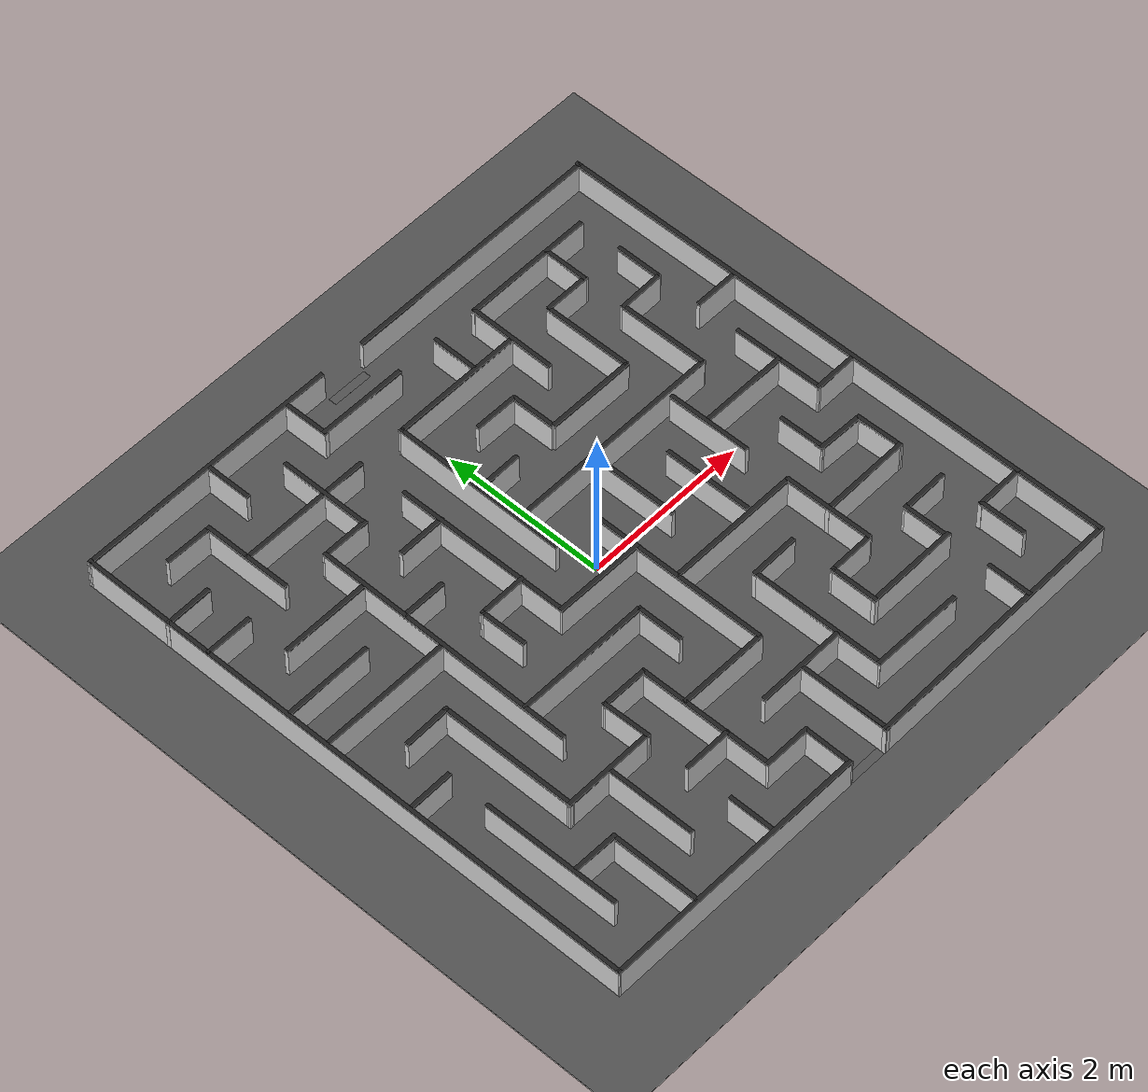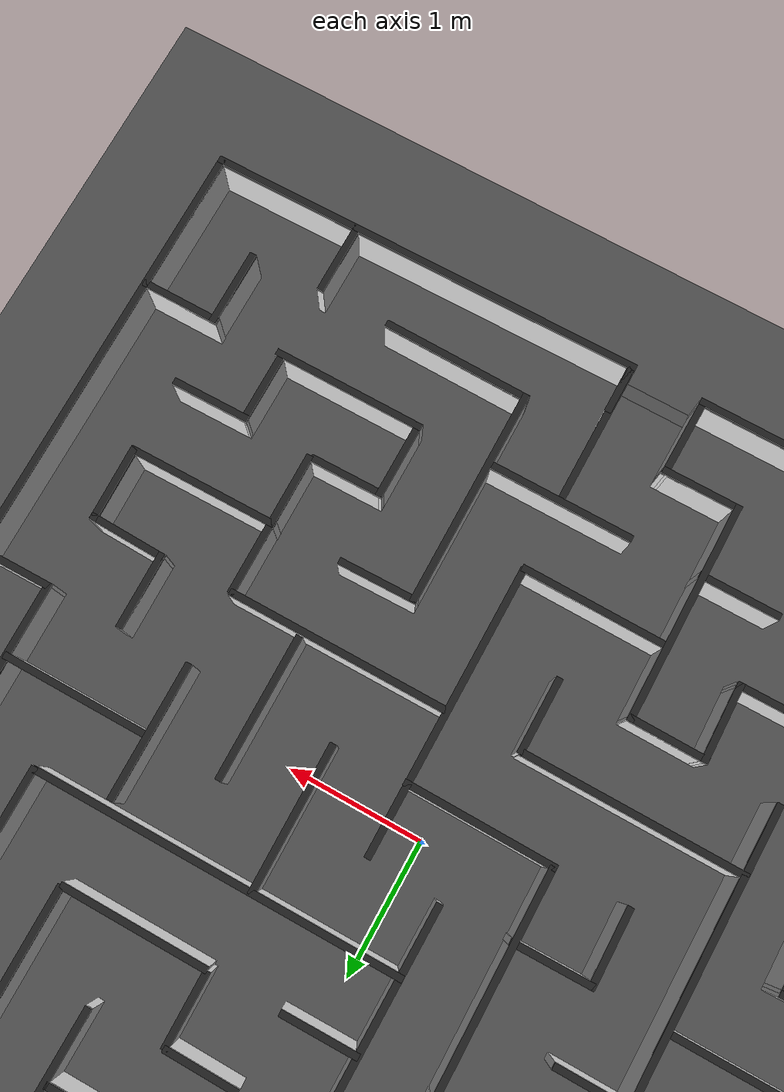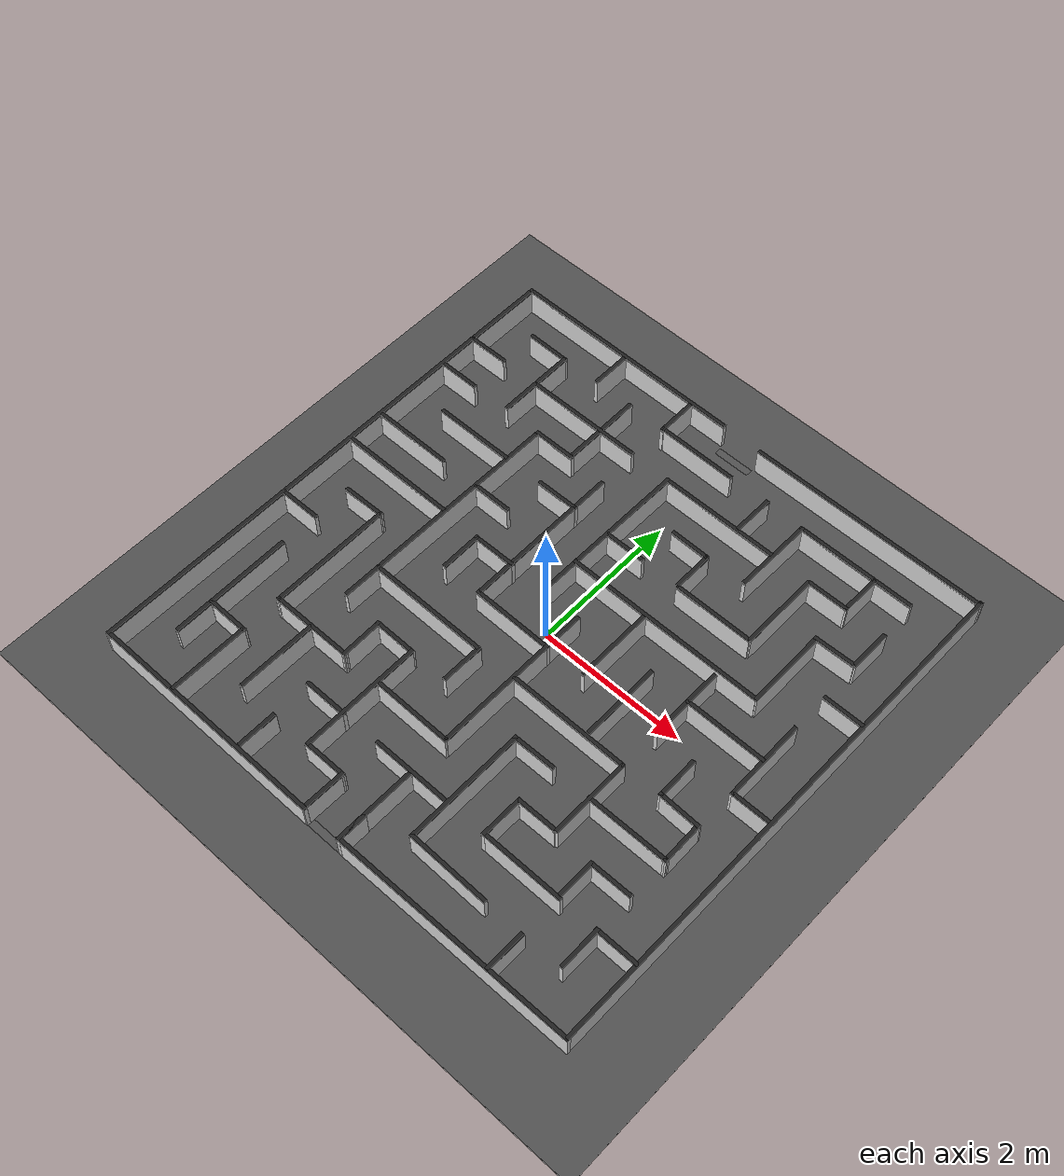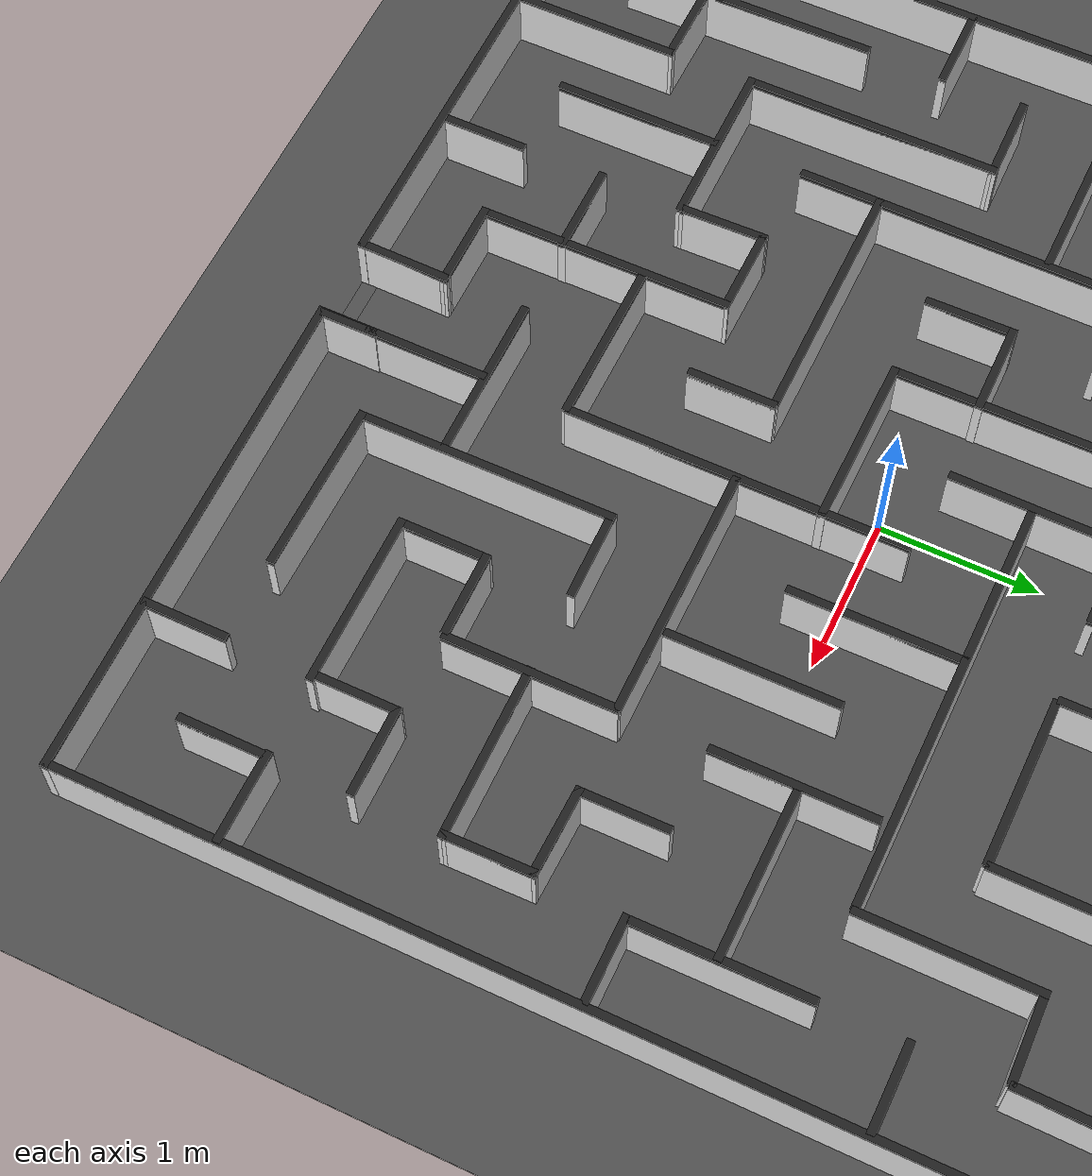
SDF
<sdf version="1.6">
 <world name="default">
  <light name="sun" type="directional">
   <pose>0 0 10 0 -0 0</pose>
   <diffuse>0.8 0.8 0.8 1</diffuse>
   <specular>0.1 0.1 0.1 1</specular>
   <attenuation>
    <range>1000</range>
    <constant>0.9</constant>
    <linear>0.01</linear>
    <quadratic>0.001</quadratic>
   </attenuation>
   <direction>-0.5 0.5 -1</direction>
  </light>
  <model name="ground_plane">
   <static>1</static>
   <link name="link">
    <collision name="collision">
     <geometry><plane><normal>0 0 1</normal><size>100 100</size></plane></geometry>
     <surface><friction><ode><mu>100</mu><mu2>50</mu2></ode></friction></surface>
    </collision>
    <visual name="visual">
     <cast_shadows>0</cast_shadows>
     <geometry><plane><normal>0 0 1</normal><size>100 100</size></plane></geometry>
     <material>
      <script><uri>file://media/materials/scripts/gazebo.material</uri><name>Gazebo/Grey</name></script>
     </material>
    </visual>
   </link>
  </model>
  <gravity>0 0 -9.8</gravity>
  <magnetic_field>6e-06 2.3e-05 -4.2e-05</magnetic_field>
  <atmosphere type="adiabatic"/>
  <physics name="default_physics" default="0" type="ode">
   <max_step_size>0.001</max_step_size>
   <real_time_factor>1</real_time_factor>
   <real_time_update_rate>1000</real_time_update_rate>
  </physics>
  <scene><ambient>0.4 0.4 0.4 1</ambient><background>0.7 0.7 0.7 1</background><shadows>1</shadows></scene>
  <spherical_coordinates>
   <surface_model>EARTH_WGS84</surface_model>
   <latitude_deg>0</latitude_deg>
   <longitude_deg>0</longitude_deg>
   <elevation>0</elevation>
   <heading_deg>0</heading_deg>
  </spherical_coordinates>
  <model name="ibo2maze">
   <link name="Wall_0">
    <collision name="Wall_0_Collision">
     <geometry><box><size>7.05733 0.05 0.37</size></box></geometry>
     <pose>0 0 0.185 0 -0 0</pose>
    </collision>
    <visual name="Wall_0_Visual">
     <pose>0 0 0.185 0 -0 0</pose>
     <geometry><box><size>7.05733 0.05 0.37</size></box></geometry>
     <material>
      <script><uri>file://media/materials/scripts/gazebo.material</uri><name>Gazebo/White</name></script>
      <ambient>1 1 1 1</ambient>
     </material>
    </visual>
    <pose>-3.50243 -0.007222 0 0 0 -1.56961</pose>
   </link>
   <link name="Wall_10">
    <collision name="Wall_10_Collision">
     <geometry><box><size>0.54316 0.05 0.37</size></box></geometry>
     <pose>0 0 0.185 0 -0 0</pose>
    </collision>
    <visual name="Wall_10_Visual">
     <pose>0 0 0.185 0 -0 0</pose>
     <geometry><box><size>0.54316 0.05 0.37</size></box></geometry>
     <material>
      <script><uri>file://media/materials/scripts/gazebo.material</uri><name>Gazebo/White</name></script>
      <ambient>1 1 1 1</ambient>
     </material>
    </visual>
    <pose>2.41673 -3.23138 0 0 0 -1.5708</pose>
   </link>
   <link name="Wall_101">
    <collision name="Wall_101_Collision">
     <geometry><box><size>1.08875 0.05 0.37</size></box></geometry>
     <pose>0 0 0.185 0 -0 0</pose>
    </collision>
    <visual name="Wall_101_Visual">
     <pose>0 0 0.185 0 -0 0</pose>
     <geometry><box><size>1.08875 0.05 0.37</size></box></geometry>
     <material>
      <script><uri>file://media/materials/scripts/gazebo.material</uri><name>Gazebo/White</name></script>
      <ambient>1 1 1 1</ambient>
     </material>
    </visual>
    <pose>1.88723 -1.34738 0 0 0 -1.56598</pose>
   </link>
   <link name="Wall_103">
    <collision name="Wall_103_Collision">
     <geometry><box><size>0.557084 0.05 0.37</size></box></geometry>
     <pose>0 0 0.185 0 -0 0</pose>
    </collision>
    <visual name="Wall_103_Visual">
     <pose>0 0 0.185 0 -0 0</pose>
     <geometry><box><size>0.557084 0.05 0.37</size></box></geometry>
     <material>
      <script><uri>file://media/materials/scripts/gazebo.material</uri><name>Gazebo/White</name></script>
      <ambient>1 1 1 1</ambient>
     </material>
    </visual>
    <pose>1.60123 -1.88438 0 0 -0 0.009862</pose>
   </link>
   <link name="Wall_105">
    <collision name="Wall_105_Collision">
     <geometry><box><size>0.587023 0.05 0.37</size></box></geometry>
     <pose>0 0 0.185 0 -0 0</pose>
    </collision>
    <visual name="Wall_105_Visual">
     <pose>0 0 0.185 0 -0 0</pose>
     <geometry><box><size>0.587023 0.05 0.37</size></box></geometry>
     <material>
      <script><uri>file://media/materials/scripts/gazebo.material</uri><name>Gazebo/White</name></script>
      <ambient>1 1 1 1</ambient>
     </material>
    </visual>
    <pose>1.34773 -2.15538 0 0 -0 1.5708</pose>
   </link>
   <link name="Wall_107">
    <collision name="Wall_107_Collision">
     <geometry><box><size>1.13403 0.05 0.37</size></box></geometry>
     <pose>0 0 0.185 0 -0 0</pose>
    </collision>
    <visual name="Wall_107_Visual">
     <pose>0 0 0.185 0 -0 0</pose>
     <geometry><box><size>1.13403 0.05 0.37</size></box></geometry>
     <material>
      <script><uri>file://media/materials/scripts/gazebo.material</uri><name>Gazebo/White</name></script>
      <ambient>1 1 1 1</ambient>
     </material>
    </visual>
    <pose>1.88973 -2.42388 0 0 -0 3.14159</pose>
   </link>
   <link name="Wall_109">
    <collision name="Wall_109_Collision">
     <geometry><box><size>0.521835 0.05 0.37</size></box></geometry>
     <pose>0 0 0.185 0 -0 0</pose>
    </collision>
    <visual name="Wall_109_Visual">
     <pose>0 0 0.185 0 -0 0</pose>
     <geometry><box><size>0.521835 0.05 0.37</size></box></geometry>
     <material>
      <script><uri>file://media/materials/scripts/gazebo.material</uri><name>Gazebo/White</name></script>
      <ambient>1 1 1 1</ambient>
     </material>
    </visual>
    <pose>2.41173 -2.14288 0 0 0 -1.5708</pose>
   </link>
   <link name="Wall_111">
    <collision name="Wall_111_Collision">
     <geometry><box><size>0.582023 0.05 0.37</size></box></geometry>
     <pose>0 0 0.185 0 -0 0</pose>
    </collision>
    <visual name="Wall_111_Visual">
     <pose>0 0 0.185 0 -0 0</pose>
     <geometry><box><size>0.582023 0.05 0.37</size></box></geometry>
     <material>
      <script><uri>file://media/materials/scripts/gazebo.material</uri><name>Gazebo/White</name></script>
      <ambient>1 1 1 1</ambient>
     </material>
    </visual>
    <pose>2.67773 -1.90438 0 0 0 -3.13219</pose>
   </link>
   <link name="Wall_113">
    <collision name="Wall_113_Collision">
     <geometry><box><size>1.641 0.05 0.37</size></box></geometry>
     <pose>0 0 0.185 0 -0 0</pose>
    </collision>
    <visual name="Wall_113_Visual">
     <pose>0 0 0.185 0 -0 0</pose>
     <geometry><box><size>1.641 0.05 0.37</size></box></geometry>
     <material>
      <script><uri>file://media/materials/scripts/gazebo.material</uri><name>Gazebo/White</name></script>
      <ambient>1 1 1 1</ambient>
     </material>
    </visual>
    <pose>1.07523 -0.817883 0 0 -0 0</pose>
   </link>
   <link name="Wall_115">
    <collision name="Wall_115_Collision">
     <geometry><box><size>1.07453 0.05 0.37</size></box></geometry>
     <pose>0 0 0.185 0 -0 0</pose>
    </collision>
    <visual name="Wall_115_Visual">
     <pose>0 0 0.185 0 -0 0</pose>
     <geometry><box><size>1.07453 0.05 0.37</size></box></geometry>
     <material>
      <script><uri>file://media/materials/scripts/gazebo.material</uri><name>Gazebo/White</name></script>
      <ambient>1 1 1 1</ambient>
     </material>
    </visual>
    <pose>1.34073 -0.245383 0 0 0 -1.56689</pose>
   </link>
   <link name="Wall_117">
    <collision name="Wall_117_Collision">
     <geometry><box><size>1.63678 0.05 0.37</size></box></geometry>
     <pose>0 0 0.185 0 -0 0</pose>
    </collision>
    <visual name="Wall_117_Visual">
     <pose>0 0 0.185 0 -0 0</pose>
     <geometry><box><size>1.63678 0.05 0.37</size></box></geometry>
     <material>
      <script><uri>file://media/materials/scripts/gazebo.material</uri><name>Gazebo/White</name></script>
      <ambient>1 1 1 1</ambient>
     </material>
    </visual>
    <pose>-1.10477 -0.814883 0 0 0 -0.00252</pose>
   </link>
   <link name="Wall_119">
    <collision name="Wall_119_Collision">
     <geometry><box><size>0.567358 0.05 0.37</size></box></geometry>
     <pose>0 0 0.185 0 -0 0</pose>
    </collision>
    <visual name="Wall_119_Visual">
     <pose>0 0 0.185 0 -0 0</pose>
     <geometry><box><size>0.567358 0.05 0.37</size></box></geometry>
     <material>
      <script><uri>file://media/materials/scripts/gazebo.material</uri><name>Gazebo/White</name></script>
      <ambient>1 1 1 1</ambient>
     </material>
    </visual>
    <pose>-0.287391 -1.08343 0 0 -0 1.5708</pose>
   </link>
   <link name="Wall_12">
    <collision name="Wall_12_Collision">
     <geometry><box><size>0.595301 0.05 0.37</size></box></geometry>
     <pose>0 0 0.185 0 -0 0</pose>
    </collision>
    <visual name="Wall_12_Visual">
     <pose>0 0 0.185 0 -0 0</pose>
     <geometry><box><size>0.595301 0.05 0.37</size></box></geometry>
     <material>
      <script><uri>file://media/materials/scripts/gazebo.material</uri><name>Gazebo/White</name></script>
      <ambient>1 1 1 1</ambient>
     </material>
    </visual>
    <pose>3.22266 -2.41896 0 0 0 -0.000276</pose>
   </link>
   <link name="Wall_121">
    <collision name="Wall_121_Collision">
     <geometry><box><size>0.573974 0.05 0.37</size></box></geometry>
     <pose>0 0 0.185 0 -0 0</pose>
    </collision>
    <visual name="Wall_121_Visual">
     <pose>0 0 0.185 0 -0 0</pose>
     <geometry><box><size>0.573974 0.05 0.37</size></box></geometry>
     <material>
      <script><uri>file://media/materials/scripts/gazebo.material</uri><name>Gazebo/White</name></script>
      <ambient>1 1 1 1</ambient>
     </material>
    </visual>
    <pose>-3.24527 2.41116 0 0 -0 0.0113</pose>
   </link>
   <link name="Wall_123">
    <collision name="Wall_123_Collision">
     <geometry><box><size>0.576958 0.05 0.37</size></box></geometry>
     <pose>0 0 0.185 0 -0 0</pose>
    </collision>
    <visual name="Wall_123_Visual">
     <pose>0 0 0.185 0 -0 0</pose>
     <geometry><box><size>0.576958 0.05 0.37</size></box></geometry>
     <material>
      <script><uri>file://media/materials/scripts/gazebo.material</uri><name>Gazebo/White</name></script>
      <ambient>1 1 1 1</ambient>
     </material>
    </visual>
    <pose>-3.22577 1.87312 0 0 -0 3.14159</pose>
   </link>
   <link name="Wall_125">
    <collision name="Wall_125_Collision">
     <geometry><box><size>1.09238 0.05 0.37</size></box></geometry>
     <pose>0 0 0.185 0 -0 0</pose>
    </collision>
    <visual name="Wall_125_Visual">
     <pose>0 0 0.185 0 -0 0</pose>
     <geometry><box><size>1.09238 0.05 0.37</size></box></geometry>
     <material>
      <script><uri>file://media/materials/scripts/gazebo.material</uri><name>Gazebo/White</name></script>
      <ambient>1 1 1 1</ambient>
     </material>
    </visual>
    <pose>-2.43527 1.33762 0 0 -0 0.002879</pose>
   </link>
   <link name="Wall_127">
    <collision name="Wall_127_Collision">
     <geometry><box><size>1.064 0.05 0.37</size></box></geometry>
     <pose>0 0 0.185 0 -0 0</pose>
    </collision>
    <visual name="Wall_127_Visual">
     <pose>0 0 0.185 0 -0 0</pose>
     <geometry><box><size>1.064 0.05 0.37</size></box></geometry>
     <material>
      <script><uri>file://media/materials/scripts/gazebo.material</uri><name>Gazebo/White</name></script>
      <ambient>1 1 1 1</ambient>
     </material>
    </visual>
    <pose>-2.95358 0.792772 0 0 -0 0</pose>
   </link>
   <link name="Wall_129">
    <collision name="Wall_129_Collision">
     <geometry><box><size>1.08471 0.05 0.37</size></box></geometry>
     <pose>0 0 0.185 0 -0 0</pose>
    </collision>
    <visual name="Wall_129_Visual">
     <pose>0 0 0.185 0 -0 0</pose>
     <geometry><box><size>1.08471 0.05 0.37</size></box></geometry>
     <material>
      <script><uri>file://media/materials/scripts/gazebo.material</uri><name>Gazebo/White</name></script>
      <ambient>1 1 1 1</ambient>
     </material>
    </visual>
    <pose>-2.42749 2.42492 0 0 0 -1.56456</pose>
   </link>
   <link name="Wall_131">
    <collision name="Wall_131_Collision">
     <geometry><box><size>1.61554 0.05 0.37</size></box></geometry>
     <pose>0 0 0.185 0 -0 0</pose>
    </collision>
    <visual name="Wall_131_Visual">
     <pose>0 0 0.185 0 -0 0</pose>
     <geometry><box><size>1.61554 0.05 0.37</size></box></geometry>
     <material>
      <script><uri>file://media/materials/scripts/gazebo.material</uri><name>Gazebo/White</name></script>
      <ambient>1 1 1 1</ambient>
     </material>
    </visual>
    <pose>-1.63727 2.41312 0 0 -0 0.002554</pose>
   </link>
   <link name="Wall_133">
    <collision name="Wall_133_Collision">
     <geometry><box><size>1.08315 0.05 0.37</size></box></geometry>
     <pose>0 0 0.185 0 -0 0</pose>
    </collision>
    <visual name="Wall_133_Visual">
     <pose>0 0 0.185 0 -0 0</pose>
     <geometry><box><size>1.08315 0.05 0.37</size></box></geometry>
     <material>
      <script><uri>file://media/materials/scripts/gazebo.material</uri><name>Gazebo/White</name></script>
      <ambient>1 1 1 1</ambient>
     </material>
    </visual>
    <pose>-1.35127 2.42862 0 0 0 -1.5708</pose>
   </link>
   <link name="Wall_135">
    <collision name="Wall_135_Collision">
     <geometry><box><size>0.589877 0.05 0.37</size></box></geometry>
     <pose>0 0 0.185 0 -0 0</pose>
    </collision>
    <visual name="Wall_135_Visual">
     <pose>0 0 0.185 0 -0 0</pose>
     <geometry><box><size>0.589877 0.05 0.37</size></box></geometry>
     <material>
      <script><uri>file://media/materials/scripts/gazebo.material</uri><name>Gazebo/White</name></script>
      <ambient>1 1 1 1</ambient>
     </material>
    </visual>
    <pose>-1.61501 1.87411 0 0 -0 0.002618</pose>
   </link>
   <link name="Wall_137">
    <collision name="Wall_137_Collision">
     <geometry><box><size>0.547 0.05 0.37</size></box></geometry>
     <pose>0 0 0.185 0 -0 0</pose>
    </collision>
    <visual name="Wall_137_Visual">
     <pose>0 0 0.185 0 -0 0</pose>
     <geometry><box><size>0.547 0.05 0.37</size></box></geometry>
     <material>
      <script><uri>file://media/materials/scripts/gazebo.material</uri><name>Gazebo/White</name></script>
      <ambient>1 1 1 1</ambient>
     </material>
    </visual>
    <pose>-1.89527 3.20862 0 0 -0 1.5708</pose>
   </link>
   <link name="Wall_139">
    <collision name="Wall_139_Collision">
     <geometry><box><size>0.555797 0.05 0.37</size></box></geometry>
     <pose>0 0 0.185 0 -0 0</pose>
    </collision>
    <visual name="Wall_139_Visual">
     <pose>0 0 0.185 0 -0 0</pose>
     <geometry><box><size>0.555797 0.05 0.37</size></box></geometry>
     <material>
      <script><uri>file://media/materials/scripts/gazebo.material</uri><name>Gazebo/White</name></script>
      <ambient>1 1 1 1</ambient>
     </material>
    </visual>
    <pose>-0.808266 3.19612 0 0 -0 1.5787</pose>
   </link>
   <link name="Wall_14">
    <collision name="Wall_14_Collision">
     <geometry><box><size>0.57685 0.05 0.37</size></box></geometry>
     <pose>0 0 0.185 0 -0 0</pose>
    </collision>
    <visual name="Wall_14_Visual">
     <pose>0 0 0.185 0 -0 0</pose>
     <geometry><box><size>0.57685 0.05 0.37</size></box></geometry>
     <material>
      <script><uri>file://media/materials/scripts/gazebo.material</uri><name>Gazebo/White</name></script>
      <ambient>1 1 1 1</ambient>
     </material>
    </visual>
    <pose>2.95658 -2.68238 0 0 -0 1.5708</pose>
   </link>
   <link name="Wall_141">
    <collision name="Wall_141_Collision">
     <geometry><box><size>1.10075 0.05 0.37</size></box></geometry>
     <pose>0 0 0.185 0 -0 0</pose>
    </collision>
    <visual name="Wall_141_Visual">
     <pose>0 0 0.185 0 -0 0</pose>
     <geometry><box><size>1.10075 0.05 0.37</size></box></geometry>
     <material>
      <script><uri>file://media/materials/scripts/gazebo.material</uri><name>Gazebo/White</name></script>
      <ambient>1 1 1 1</ambient>
     </material>
    </visual>
    <pose>-0.277639 2.95138 0 0 -0 3.13728</pose>
   </link>
   <link name="Wall_143">
    <collision name="Wall_143_Collision">
     <geometry><box><size>0.595023 0.05 0.37</size></box></geometry>
     <pose>0 0 0.185 0 -0 0</pose>
    </collision>
    <visual name="Wall_143_Visual">
     <pose>0 0 0.185 0 -0 0</pose>
     <geometry><box><size>0.595023 0.05 0.37</size></box></geometry>
     <material>
      <script><uri>file://media/materials/scripts/gazebo.material</uri><name>Gazebo/White</name></script>
      <ambient>1 1 1 1</ambient>
     </material>
    </visual>
    <pose>-2.70322 2.94477 0 0 0 -0.009174</pose>
   </link>
   <link name="Wall_145">
    <collision name="Wall_145_Collision">
     <geometry><box><size>1.62601 0.05 0.37</size></box></geometry>
     <pose>0 0 0.185 0 -0 0</pose>
    </collision>
    <visual name="Wall_145_Visual">
     <pose>0 0 0.185 0 -0 0</pose>
     <geometry><box><size>1.62601 0.05 0.37</size></box></geometry>
     <material>
      <script><uri>file://media/materials/scripts/gazebo.material</uri><name>Gazebo/White</name></script>
      <ambient>1 1 1 1</ambient>
     </material>
    </visual>
    <pose>0.52279 2.4088 0 0 -0 0.003807</pose>
   </link>
   <link name="Wall_147">
    <collision name="Wall_147_Collision">
     <geometry><box><size>1.07898 0.05 0.37</size></box></geometry>
     <pose>0 0 0.185 0 -0 0</pose>
    </collision>
    <visual name="Wall_147_Visual">
     <pose>0 0 0.185 0 -0 0</pose>
     <geometry><box><size>1.07898 0.05 0.37</size></box></geometry>
     <material>
      <script><uri>file://media/materials/scripts/gazebo.material</uri><name>Gazebo/White</name></script>
      <ambient>1 1 1 1</ambient>
     </material>
    </visual>
    <pose>1.34522 2.42762 0 0 0 -1.5834</pose>
   </link>
   <link name="Wall_149">
    <collision name="Wall_149_Collision">
     <geometry><box><size>1.62001 0.05 0.37</size></box></geometry>
     <pose>0 0 0.185 0 -0 0</pose>
    </collision>
    <visual name="Wall_149_Visual">
     <pose>0 0 0.185 0 -0 0</pose>
     <geometry><box><size>1.62001 0.05 0.37</size></box></geometry>
     <material>
      <script><uri>file://media/materials/scripts/gazebo.material</uri><name>Gazebo/White</name></script>
      <ambient>1 1 1 1</ambient>
     </material>
    </visual>
    <pose>2.13238 2.94459 0 0 -0 0.003185</pose>
   </link>
   <link name="Wall_151">
    <collision name="Wall_151_Collision">
     <geometry><box><size>0.560016 0.05 0.37</size></box></geometry>
     <pose>0 0 0.185 0 -0 0</pose>
    </collision>
    <visual name="Wall_151_Visual">
     <pose>0 0 0.185 0 -0 0</pose>
     <geometry><box><size>0.560016 0.05 0.37</size></box></geometry>
     <material>
      <script><uri>file://media/materials/scripts/gazebo.material</uri><name>Gazebo/White</name></script>
      <ambient>1 1 1 1</ambient>
     </material>
    </visual>
    <pose>2.41773 2.67012 0 0 -0 1.56295</pose>
   </link>
   <link name="Wall_153">
    <collision name="Wall_153_Collision">
     <geometry><box><size>0.573013 0.05 0.37</size></box></geometry>
     <pose>0 0 0.185 0 -0 0</pose>
    </collision>
    <visual name="Wall_153_Visual">
     <pose>0 0 0.185 0 -0 0</pose>
     <geometry><box><size>0.573013 0.05 0.37</size></box></geometry>
     <material>
      <script><uri>file://media/materials/scripts/gazebo.material</uri><name>Gazebo/White</name></script>
      <ambient>1 1 1 1</ambient>
     </material>
    </visual>
    <pose>2.15423 2.41312 0 0 -0 0.007648</pose>
   </link>
   <link name="Wall_155">
    <collision name="Wall_155_Collision">
     <geometry><box><size>1.08393 0.05 0.37</size></box></geometry>
     <pose>0 0 0.185 0 -0 0</pose>
    </collision>
    <visual name="Wall_155_Visual">
     <pose>0 0 0.185 0 -0 0</pose>
     <geometry><box><size>1.08393 0.05 0.37</size></box></geometry>
     <material>
      <script><uri>file://media/materials/scripts/gazebo.material</uri><name>Gazebo/White</name></script>
      <ambient>1 1 1 1</ambient>
     </material>
    </visual>
    <pose>1.87888 1.87677 0 0 -0 1.56989</pose>
   </link>
   <link name="Wall_157">
    <collision name="Wall_157_Collision">
     <geometry><box><size>1.084 0.05 0.37</size></box></geometry>
     <pose>0 0 0.185 0 -0 0</pose>
    </collision>
    <visual name="Wall_157_Visual">
     <pose>0 0 0.185 0 -0 0</pose>
     <geometry><box><size>1.084 0.05 0.37</size></box></geometry>
     <material>
      <script><uri>file://media/materials/scripts/gazebo.material</uri><name>Gazebo/White</name></script>
      <ambient>1 1 1 1</ambient>
     </material>
    </visual>
    <pose>1.3441 1.34012 0 0 -0 0</pose>
   </link>
   <link name="Wall_159">
    <collision name="Wall_159_Collision">
     <geometry><box><size>0.542009 0.05 0.37</size></box></geometry>
     <pose>0 0 0.185 0 -0 0</pose>
    </collision>
    <visual name="Wall_159_Visual">
     <pose>0 0 0.185 0 -0 0</pose>
     <geometry><box><size>0.542009 0.05 0.37</size></box></geometry>
     <material>
      <script><uri>file://media/materials/scripts/gazebo.material</uri><name>Gazebo/White</name></script>
      <ambient>1 1 1 1</ambient>
     </material>
    </visual>
    <pose>0.799706 1.61175 0 0 0 -1.5647</pose>
   </link>
   <link name="Wall_16">
    <collision name="Wall_16_Collision">
     <geometry><box><size>1.11506 0.05 0.37</size></box></geometry>
     <pose>0 0 0.185 0 -0 0</pose>
    </collision>
    <visual name="Wall_16_Visual">
     <pose>0 0 0.185 0 -0 0</pose>
     <geometry><box><size>1.11506 0.05 0.37</size></box></geometry>
     <material>
      <script><uri>file://media/materials/scripts/gazebo.material</uri><name>Gazebo/White</name></script>
      <ambient>1 1 1 1</ambient>
     </material>
    </visual>
    <pose>0.260659 -2.97838 0 0 0 -1.57094</pose>
   </link>
   <link name="Wall_161">
    <collision name="Wall_161_Collision">
     <geometry><box><size>0.539009 0.05 0.37</size></box></geometry>
     <pose>0 0 0.185 0 -0 0</pose>
    </collision>
    <visual name="Wall_161_Visual">
     <pose>0 0 0.185 0 -0 0</pose>
     <geometry><box><size>0.539009 0.05 0.37</size></box></geometry>
     <material>
      <script><uri>file://media/materials/scripts/gazebo.material</uri><name>Gazebo/White</name></script>
      <ambient>1 1 1 1</ambient>
     </material>
    </visual>
    <pose>0.537132 1.87577 0 0 0 -0.006135</pose>
   </link>
   <link name="Wall_163">
    <collision name="Wall_163_Collision">
     <geometry><box><size>0.562483 0.05 0.37</size></box></geometry>
     <pose>0 0 0.185 0 -0 0</pose>
    </collision>
    <visual name="Wall_163_Visual">
     <pose>0 0 0.185 0 -0 0</pose>
     <geometry><box><size>0.562483 0.05 0.37</size></box></geometry>
     <material>
      <script><uri>file://media/materials/scripts/gazebo.material</uri><name>Gazebo/White</name></script>
      <ambient>1 1 1 1</ambient>
     </material>
    </visual>
    <pose>-0.001266 1.33762 0 0 -0 0.009765</pose>
   </link>
   <link name="Wall_165">
    <collision name="Wall_165_Collision">
     <geometry><box><size>0.539 0.05 0.37</size></box></geometry>
     <pose>0 0 0.185 0 -0 0</pose>
    </collision>
    <visual name="Wall_165_Visual">
     <pose>0 0 0.185 0 -0 0</pose>
     <geometry><box><size>0.539 0.05 0.37</size></box></geometry>
     <material>
      <script><uri>file://media/materials/scripts/gazebo.material</uri><name>Gazebo/White</name></script>
      <ambient>1 1 1 1</ambient>
     </material>
    </visual>
    <pose>-1.62944 0.795117 0 0 -0 0</pose>
   </link>
   <link name="Wall_167">
    <collision name="Wall_167_Collision">
     <geometry><box><size>0.560258 0.05 0.37</size></box></geometry>
     <pose>0 0 0.185 0 -0 0</pose>
    </collision>
    <visual name="Wall_167_Visual">
     <pose>0 0 0.185 0 -0 0</pose>
     <geometry><box><size>0.560258 0.05 0.37</size></box></geometry>
     <material>
      <script><uri>file://media/materials/scripts/gazebo.material</uri><name>Gazebo/White</name></script>
      <ambient>1 1 1 1</ambient>
     </material>
    </visual>
    <pose>0.804234 2.70212 0 0 0 -1.5806</pose>
   </link>
   <link name="Wall_169">
    <collision name="Wall_169_Collision">
     <geometry><box><size>0.556215 0.05 0.37</size></box></geometry>
     <pose>0 0 0.185 0 -0 0</pose>
    </collision>
    <visual name="Wall_169_Visual">
     <pose>0 0 0.185 0 -0 0</pose>
     <geometry><box><size>0.556215 0.05 0.37</size></box></geometry>
     <material>
      <script><uri>file://media/materials/scripts/gazebo.material</uri><name>Gazebo/White</name></script>
      <ambient>1 1 1 1</ambient>
     </material>
    </visual>
    <pose>3.22073 1.33612 0 0 -0 0</pose>
   </link>
   <link name="Wall_17">
    <collision name="Wall_17_Collision">
     <geometry><box><size>0.400275 0.05 0.37</size></box></geometry>
     <pose>0 0 0.185 0 -0 0</pose>
    </collision>
    <visual name="Wall_17_Visual">
     <pose>0 0 0.185 0 -0 0</pose>
     <geometry><box><size>0.400275 0.05 0.37</size></box></geometry>
     <material>
      <script><uri>file://media/materials/scripts/gazebo.material</uri><name>Gazebo/White</name></script>
      <ambient>1 1 1 1</ambient>
     </material>
    </visual>
    <pose>0.267159 -3.33588 0 0 -0 1.5708</pose>
   </link>
   <link name="Wall_171">
    <collision name="Wall_171_Collision">
     <geometry><box><size>0.563985 0.05 0.37</size></box></geometry>
     <pose>0 0 0.185 0 -0 0</pose>
    </collision>
    <visual name="Wall_171_Visual">
     <pose>0 0 0.185 0 -0 0</pose>
     <geometry><box><size>0.563985 0.05 0.37</size></box></geometry>
     <material>
      <script><uri>file://media/materials/scripts/gazebo.material</uri><name>Gazebo/White</name></script>
      <ambient>1 1 1 1</ambient>
     </material>
    </visual>
    <pose>2.95273 2.15912 0 0 0 -1.57858</pose>
   </link>
   <link name="Wall_173">
    <collision name="Wall_173_Collision">
     <geometry><box><size>0.563271 0.05 0.37</size></box></geometry>
     <pose>0 0 0.185 0 -0 0</pose>
    </collision>
    <visual name="Wall_173_Visual">
     <pose>0 0 0.185 0 -0 0</pose>
     <geometry><box><size>0.563271 0.05 0.37</size></box></geometry>
     <material>
      <script><uri>file://media/materials/scripts/gazebo.material</uri><name>Gazebo/White</name></script>
      <ambient>1 1 1 1</ambient>
     </material>
    </visual>
    <pose>2.67215 1.8782 0 0 -0 0.02693</pose>
   </link>
   <link name="Wall_175">
    <collision name="Wall_175_Collision">
     <geometry><box><size>1.11244 0.05 0.37</size></box></geometry>
     <pose>0 0 0.185 0 -0 0</pose>
    </collision>
    <visual name="Wall_175_Visual">
     <pose>0 0 0.185 0 -0 0</pose>
     <geometry><box><size>1.11244 0.05 0.37</size></box></geometry>
     <material>
      <script><uri>file://media/materials/scripts/gazebo.material</uri><name>Gazebo/White</name></script>
      <ambient>1 1 1 1</ambient>
     </material>
    </visual>
    <pose>2.41721 1.34008 0 0 0 -1.56772</pose>
   </link>
   <link name="Wall_19">
    <collision name="Wall_19_Collision">
     <geometry><box><size>1.08267 0.05 0.37</size></box></geometry>
     <pose>0 0 0.185 0 -0 0</pose>
    </collision>
    <visual name="Wall_19_Visual">
     <pose>0 0 0.185 0 -0 0</pose>
     <geometry><box><size>1.08267 0.05 0.37</size></box></geometry>
     <material>
      <script><uri>file://media/materials/scripts/gazebo.material</uri><name>Gazebo/White</name></script>
      <ambient>1 1 1 1</ambient>
     </material>
    </visual>
    <pose>0.257234 -2.42588 0 0 -0 0</pose>
   </link>
   <link name="Wall_2">
    <collision name="Wall_2_Collision">
     <geometry><box><size>3.248 0.05 0.37</size></box></geometry>
     <pose>0 0 0.185 0 -0 0</pose>
    </collision>
    <visual name="Wall_2_Visual">
     <pose>0 0 0.185 0 -0 0</pose>
     <geometry><box><size>3.248 0.05 0.37</size></box></geometry>
     <material>
      <script><uri>file://media/materials/scripts/gazebo.material</uri><name>Gazebo/White</name></script>
      <ambient>1 1 1 1</ambient>
     </material>
    </visual>
    <pose>-1.90759 3.49394 0 0 -0 3.14003</pose>
   </link>
   <link name="Wall_21">
    <collision name="Wall_21_Collision">
     <geometry><box><size>1.64813 0.05 0.37</size></box></geometry>
     <pose>0 0 0.185 0 -0 0</pose>
    </collision>
    <visual name="Wall_21_Visual">
     <pose>0 0 0.185 0 -0 0</pose>
     <geometry><box><size>1.64813 0.05 0.37</size></box></geometry>
     <material>
      <script><uri>file://media/materials/scripts/gazebo.material</uri><name>Gazebo/White</name></script>
      <ambient>1 1 1 1</ambient>
     </material>
    </visual>
    <pose>0.803365 -2.15919 0 0 0 -1.56715</pose>
   </link>
   <link name="Wall_23">
    <collision name="Wall_23_Collision">
     <geometry><box><size>1.11554 0.05 0.37</size></box></geometry>
     <pose>0 0 0.185 0 -0 0</pose>
    </collision>
    <visual name="Wall_23_Visual">
     <pose>0 0 0.185 0 -0 0</pose>
     <geometry><box><size>1.11554 0.05 0.37</size></box></geometry>
     <material>
      <script><uri>file://media/materials/scripts/gazebo.material</uri><name>Gazebo/White</name></script>
      <ambient>1 1 1 1</ambient>
     </material>
    </visual>
    <pose>1.33901 -2.96524 0 0 -0 3.12913</pose>
   </link>
   <link name="Wall_25">
    <collision name="Wall_25_Collision">
     <geometry><box><size>0.589072 0.05 0.37</size></box></geometry>
     <pose>0 0 0.185 0 -0 0</pose>
    </collision>
    <visual name="Wall_25_Visual">
     <pose>0 0 0.185 0 -0 0</pose>
     <geometry><box><size>0.589072 0.05 0.37</size></box></geometry>
     <material>
      <script><uri>file://media/materials/scripts/gazebo.material</uri><name>Gazebo/White</name></script>
      <ambient>1 1 1 1</ambient>
     </material>
    </visual>
    <pose>1.06959 -1.35533 0 0 0 -3.12506</pose>
   </link>
   <link name="Wall_27">
    <collision name="Wall_27_Collision">
     <geometry><box><size>3.2721 0.05 0.37</size></box></geometry>
     <pose>0 0 0.185 0 -0 0</pose>
    </collision>
    <visual name="Wall_27_Visual">
     <pose>0 0 0.185 0 -0 0</pose>
     <geometry><box><size>3.2721 0.05 0.37</size></box></geometry>
     <material>
      <script><uri>file://media/materials/scripts/gazebo.material</uri><name>Gazebo/White</name></script>
      <ambient>1 1 1 1</ambient>
     </material>
    </visual>
    <pose>-1.88722 -3.51296 0 0 -0 3.14031</pose>
   </link>
   <link name="Wall_29">
    <collision name="Wall_29_Collision">
     <geometry><box><size>0.607073 0.05 0.37</size></box></geometry>
     <pose>0 0 0.185 0 -0 0</pose>
    </collision>
    <visual name="Wall_29_Visual">
     <pose>0 0 0.185 0 -0 0</pose>
     <geometry><box><size>0.607073 0.05 0.37</size></box></geometry>
     <material>
      <script><uri>file://media/materials/scripts/gazebo.material</uri><name>Gazebo/White</name></script>
      <ambient>1 1 1 1</ambient>
     </material>
    </visual>
    <pose>-0.273795 -3.23646 0 0 0 -1.58705</pose>
   </link>
   <link name="Wall_31">
    <collision name="Wall_31_Collision">
     <geometry><box><size>0.589035 0.05 0.37</size></box></geometry>
     <pose>0 0 0.185 0 -0 0</pose>
    </collision>
    <visual name="Wall_31_Visual">
     <pose>0 0 0.185 0 -0 0</pose>
     <geometry><box><size>0.589035 0.05 0.37</size></box></geometry>
     <material>
      <script><uri>file://media/materials/scripts/gazebo.material</uri><name>Gazebo/White</name></script>
      <ambient>1 1 1 1</ambient>
     </material>
    </visual>
    <pose>-0.538766 -2.95788 0 0 -0 0</pose>
   </link>
   <link name="Wall_33">
    <collision name="Wall_33_Collision">
     <geometry><box><size>1.65258 0.05 0.37</size></box></geometry>
     <pose>0 0 0.185 0 -0 0</pose>
    </collision>
    <visual name="Wall_33_Visual">
     <pose>0 0 0.185 0 -0 0</pose>
     <geometry><box><size>1.65258 0.05 0.37</size></box></geometry>
     <material>
      <script><uri>file://media/materials/scripts/gazebo.material</uri><name>Gazebo/White</name></script>
      <ambient>1 1 1 1</ambient>
     </material>
    </visual>
    <pose>-0.811266 -2.15638 0 0 0 -1.56705</pose>
   </link>
   <link name="Wall_35">
    <collision name="Wall_35_Collision">
     <geometry><box><size>0.537019 0.05 0.37</size></box></geometry>
     <pose>0 0 0.185 0 -0 0</pose>
    </collision>
    <visual name="Wall_35_Visual">
     <pose>0 0 0.185 0 -0 0</pose>
     <geometry><box><size>0.537019 0.05 0.37</size></box></geometry>
     <material>
      <script><uri>file://media/materials/scripts/gazebo.material</uri><name>Gazebo/White</name></script>
      <ambient>1 1 1 1</ambient>
     </material>
    </visual>
    <pose>-1.34727 -3.21538 0 0 0 -1.5708</pose>
   </link>
   <link name="Wall_37">
    <collision name="Wall_37_Collision">
     <geometry><box><size>1.08932 0.05 0.37</size></box></geometry>
     <pose>0 0 0.185 0 -0 0</pose>
    </collision>
    <visual name="Wall_37_Visual">
     <pose>0 0 0.185 0 -0 0</pose>
     <geometry><box><size>1.08932 0.05 0.37</size></box></geometry>
     <material>
      <script><uri>file://media/materials/scripts/gazebo.material</uri><name>Gazebo/White</name></script>
      <ambient>1 1 1 1</ambient>
     </material>
    </visual>
    <pose>-2.41827 -2.96538 0 0 0 -1.5708</pose>
   </link>
   <link name="Wall_39">
    <collision name="Wall_39_Collision">
     <geometry><box><size>0.583034 0.05 0.37</size></box></geometry>
     <pose>0 0 0.185 0 -0 0</pose>
    </collision>
    <visual name="Wall_39_Visual">
     <pose>0 0 0.185 0 -0 0</pose>
     <geometry><box><size>0.583034 0.05 0.37</size></box></geometry>
     <material>
      <script><uri>file://media/materials/scripts/gazebo.material</uri><name>Gazebo/White</name></script>
      <ambient>1 1 1 1</ambient>
     </material>
    </visual>
    <pose>-2.68477 -2.44288 0 0 0 -0.011257</pose>
   </link>
   <link name="Wall_4">
    <collision name="Wall_4_Collision">
     <geometry><box><size>3.27061 0.05 0.37</size></box></geometry>
     <pose>0 0 0.185 0 -0 0</pose>
    </collision>
    <visual name="Wall_4_Visual">
     <pose>0 0 0.185 0 -0 0</pose>
     <geometry><box><size>3.27061 0.05 0.37</size></box></geometry>
     <material>
      <script><uri>file://media/materials/scripts/gazebo.material</uri><name>Gazebo/White</name></script>
      <ambient>1 1 1 1</ambient>
     </material>
    </visual>
    <pose>1.89021 3.48914 0 0 0 -3.13619</pose>
   </link>
   <link name="Wall_41">
    <collision name="Wall_41_Collision">
     <geometry><box><size>1.65369 0.05 0.37</size></box></geometry>
     <pose>0 0 0.185 0 -0 0</pose>
    </collision>
    <visual name="Wall_41_Visual">
     <pose>0 0 0.185 0 -0 0</pose>
     <geometry><box><size>1.65369 0.05 0.37</size></box></geometry>
     <material>
      <script><uri>file://media/materials/scripts/gazebo.material</uri><name>Gazebo/White</name></script>
      <ambient>1 1 1 1</ambient>
     </material>
    </visual>
    <pose>-2.96548 -2.14372 0 0 0 -1.56358</pose>
   </link>
   <link name="Wall_43">
    <collision name="Wall_43_Collision">
     <geometry><box><size>1.076 0.05 0.37</size></box></geometry>
     <pose>0 0 0.185 0 -0 0</pose>
    </collision>
    <visual name="Wall_43_Visual">
     <pose>0 0 0.185 0 -0 0</pose>
     <geometry><box><size>1.076 0.05 0.37</size></box></geometry>
     <material>
      <script><uri>file://media/materials/scripts/gazebo.material</uri><name>Gazebo/White</name></script>
      <ambient>1 1 1 1</ambient>
     </material>
    </visual>
    <pose>-1.88512 -2.42403 0 0 0 -1.5708</pose>
   </link>
   <link name="Wall_45">
    <collision name="Wall_45_Collision">
     <geometry><box><size>1.12959 0.05 0.37</size></box></geometry>
     <pose>0 0 0.185 0 -0 0</pose>
    </collision>
    <visual name="Wall_45_Visual">
     <pose>0 0 0.185 0 -0 0</pose>
     <geometry><box><size>1.12959 0.05 0.37</size></box></geometry>
     <material>
      <script><uri>file://media/materials/scripts/gazebo.material</uri><name>Gazebo/White</name></script>
      <ambient>1 1 1 1</ambient>
     </material>
    </visual>
    <pose>-1.88447 -1.89026 0 0 -0 0.003006</pose>
   </link>
   <link name="Wall_47">
    <collision name="Wall_47_Collision">
     <geometry><box><size>1.67016 0.05 0.37</size></box></geometry>
     <pose>0 0 0.185 0 -0 0</pose>
    </collision>
    <visual name="Wall_47_Visual">
     <pose>0 0 0.185 0 -0 0</pose>
     <geometry><box><size>1.67016 0.05 0.37</size></box></geometry>
     <material>
      <script><uri>file://media/materials/scripts/gazebo.material</uri><name>Gazebo/White</name></script>
      <ambient>1 1 1 1</ambient>
     </material>
    </visual>
    <pose>-2.42619 -1.0818 0 0 0 -1.56842</pose>
   </link>
   <link name="Wall_49">
    <collision name="Wall_49_Collision">
     <geometry><box><size>0.58294 0.05 0.37</size></box></geometry>
     <pose>0 0 0.185 0 -0 0</pose>
    </collision>
    <visual name="Wall_49_Visual">
     <pose>0 0 0.185 0 -0 0</pose>
     <geometry><box><size>0.58294 0.05 0.37</size></box></geometry>
     <material>
      <script><uri>file://media/materials/scripts/gazebo.material</uri><name>Gazebo/White</name></script>
      <ambient>1 1 1 1</ambient>
     </material>
    </visual>
    <pose>-2.69454 -0.276627 0 0 -0 0.018403</pose>
   </link>
   <link name="Wall_51">
    <collision name="Wall_51_Collision">
     <geometry><box><size>0.558738 0.05 0.37</size></box></geometry>
     <pose>0 0 0.185 0 -0 0</pose>
    </collision>
    <visual name="Wall_51_Visual">
     <pose>0 0 0.185 0 -0 0</pose>
     <geometry><box><size>0.558738 0.05 0.37</size></box></geometry>
     <material>
      <script><uri>file://media/materials/scripts/gazebo.material</uri><name>Gazebo/White</name></script>
      <ambient>1 1 1 1</ambient>
     </material>
    </visual>
    <pose>-3.22601 -0.817592 0 0 0 -3.13332</pose>
   </link>
   <link name="Wall_53">
    <collision name="Wall_53_Collision">
     <geometry><box><size>1.58 0.05 0.37</size></box></geometry>
     <pose>0 0 0.185 0 -0 0</pose>
    </collision>
    <visual name="Wall_53_Visual">
     <pose>0 0 0.185 0 -0 0</pose>
     <geometry><box><size>1.58 0.05 0.37</size></box></geometry>
     <material>
      <script><uri>file://media/materials/scripts/gazebo.material</uri><name>Gazebo/White</name></script>
      <ambient>1 1 1 1</ambient>
     </material>
    </visual>
    <pose>-2.69484 0.278117 0 0 -0 0</pose>
   </link>
   <link name="Wall_55">
    <collision name="Wall_55_Collision">
     <geometry><box><size>3.23035 0.05 0.37</size></box></geometry>
     <pose>0 0 0.185 0 -0 0</pose>
    </collision>
    <visual name="Wall_55_Visual">
     <pose>0 0 0.185 0 -0 0</pose>
     <geometry><box><size>3.23035 0.05 0.37</size></box></geometry>
     <material>
      <script><uri>file://media/materials/scripts/gazebo.material</uri><name>Gazebo/White</name></script>
      <ambient>1 1 1 1</ambient>
     </material>
    </visual>
    <pose>-1.89511 0.283259 0 0 0 -1.57719</pose>
   </link>
   <link name="Wall_59">
    <collision name="Wall_59_Collision">
     <geometry><box><size>0.591023 0.05 0.37</size></box></geometry>
     <pose>0 0 0.185 0 -0 0</pose>
    </collision>
    <visual name="Wall_59_Visual">
     <pose>0 0 0.185 0 -0 0</pose>
     <geometry><box><size>0.591023 0.05 0.37</size></box></geometry>
     <material>
      <script><uri>file://media/materials/scripts/gazebo.material</uri><name>Gazebo/White</name></script>
      <ambient>1 1 1 1</ambient>
     </material>
    </visual>
    <pose>-1.08477 -1.35238 0 0 0 -0.009242</pose>
   </link>
   <link name="Wall_6">
    <collision name="Wall_6_Collision">
     <geometry><box><size>7.02654 0.05 0.37</size></box></geometry>
     <pose>0 0 0.185 0 -0 0</pose>
    </collision>
    <visual name="Wall_6_Visual">
     <pose>0 0 0.185 0 -0 0</pose>
     <geometry><box><size>7.02654 0.05 0.37</size></box></geometry>
     <material>
      <script><uri>file://media/materials/scripts/gazebo.material</uri><name>Gazebo/White</name></script>
      <ambient>1 1 1 1</ambient>
     </material>
    </visual>
    <pose>3.50355 0.027067 0 0 -0 1.57173</pose>
   </link>
   <link name="Wall_61">
    <collision name="Wall_61_Collision">
     <geometry><box><size>0.589024 0.05 0.37</size></box></geometry>
     <pose>0 0 0.185 0 -0 0</pose>
    </collision>
    <visual name="Wall_61_Visual">
     <pose>0 0 0.185 0 -0 0</pose>
     <geometry><box><size>0.589024 0.05 0.37</size></box></geometry>
     <material>
      <script><uri>file://media/materials/scripts/gazebo.material</uri><name>Gazebo/White</name></script>
      <ambient>1 1 1 1</ambient>
     </material>
    </visual>
    <pose>-1.34997 -1.61926 0 0 -0 1.59044</pose>
   </link>
   <link name="Wall_63">
    <collision name="Wall_63_Collision">
     <geometry><box><size>0.599 0.05 0.37</size></box></geometry>
     <pose>0 0 0.185 0 -0 0</pose>
    </collision>
    <visual name="Wall_63_Visual">
     <pose>0 0 0.185 0 -0 0</pose>
     <geometry><box><size>0.599 0.05 0.37</size></box></geometry>
     <material>
      <script><uri>file://media/materials/scripts/gazebo.material</uri><name>Gazebo/White</name></script>
      <ambient>1 1 1 1</ambient>
     </material>
    </visual>
    <pose>-1.08077 -2.42788 0 0 -0 0</pose>
   </link>
   <link name="Wall_65">
    <collision name="Wall_65_Collision">
     <geometry><box><size>1.09309 0.05 0.37</size></box></geometry>
     <pose>0 0 0.185 0 -0 0</pose>
    </collision>
    <visual name="Wall_65_Visual">
     <pose>0 0 0.185 0 -0 0</pose>
     <geometry><box><size>1.09309 0.05 0.37</size></box></geometry>
     <material>
      <script><uri>file://media/materials/scripts/gazebo.material</uri><name>Gazebo/White</name></script>
      <ambient>1 1 1 1</ambient>
     </material>
    </visual>
    <pose>-0.272766 -1.89588 0 0 0 -0.00767</pose>
   </link>
   <link name="Wall_67">
    <collision name="Wall_67_Collision">
     <geometry><box><size>2.159 0.05 0.37</size></box></geometry>
     <pose>0 0 0.185 0 -0 0</pose>
    </collision>
    <visual name="Wall_67_Visual">
     <pose>0 0 0.185 0 -0 0</pose>
     <geometry><box><size>2.159 0.05 0.37</size></box></geometry>
     <material>
      <script><uri>file://media/materials/scripts/gazebo.material</uri><name>Gazebo/White</name></script>
      <ambient>1 1 1 1</ambient>
     </material>
    </visual>
    <pose>0.256611 -0.822068 0 0 0 -1.5708</pose>
   </link>
   <link name="Wall_69">
    <collision name="Wall_69_Collision">
     <geometry><box><size>1.11615 0.05 0.37</size></box></geometry>
     <pose>0 0 0.185 0 -0 0</pose>
    </collision>
    <visual name="Wall_69_Visual">
     <pose>0 0 0.185 0 -0 0</pose>
     <geometry><box><size>1.11615 0.05 0.37</size></box></geometry>
     <material>
      <script><uri>file://media/materials/scripts/gazebo.material</uri><name>Gazebo/White</name></script>
      <ambient>1 1 1 1</ambient>
     </material>
    </visual>
    <pose>-0.273102 -0.277366 0 0 0 -0.008064</pose>
   </link>
   <link name="Wall_71">
    <collision name="Wall_71_Collision">
     <geometry><box><size>2.13701 0.05 0.37</size></box></geometry>
     <pose>0 0 0.185 0 -0 0</pose>
    </collision>
    <visual name="Wall_71_Visual">
     <pose>0 0 0.185 0 -0 0</pose>
     <geometry><box><size>2.13701 0.05 0.37</size></box></geometry>
     <material>
      <script><uri>file://media/materials/scripts/gazebo.material</uri><name>Gazebo/White</name></script>
      <ambient>1 1 1 1</ambient>
     </material>
    </visual>
    <pose>-0.811201 0.791464 0 0 0 -1.56744</pose>
   </link>
   <link name="Wall_73">
    <collision name="Wall_73_Collision">
     <geometry><box><size>0.605032 0.05 0.37</size></box></geometry>
     <pose>0 0 0.185 0 -0 0</pose>
    </collision>
    <visual name="Wall_73_Visual">
     <pose>0 0 0.185 0 -0 0</pose>
     <geometry><box><size>0.605032 0.05 0.37</size></box></geometry>
     <material>
      <script><uri>file://media/materials/scripts/gazebo.material</uri><name>Gazebo/White</name></script>
      <ambient>1 1 1 1</ambient>
     </material>
    </visual>
    <pose>-1.07977 0.262117 0 0 -0 0.01081</pose>
   </link>
   <link name="Wall_75">
    <collision name="Wall_75_Collision">
     <geometry><box><size>0.576034 0.05 0.37</size></box></geometry>
     <pose>0 0 0.185 0 -0 0</pose>
    </collision>
    <visual name="Wall_75_Visual">
     <pose>0 0 0.185 0 -0 0</pose>
     <geometry><box><size>0.576034 0.05 0.37</size></box></geometry>
     <material>
      <script><uri>file://media/materials/scripts/gazebo.material</uri><name>Gazebo/White</name></script>
      <ambient>1 1 1 1</ambient>
     </material>
    </visual>
    <pose>-1.35427 -0.003883 0 0 -0 1.5822</pose>
   </link>
   <link name="Wall_77">
    <collision name="Wall_77_Collision">
     <geometry><box><size>0.593259 0.05 0.37</size></box></geometry>
     <pose>0 0 0.185 0 -0 0</pose>
    </collision>
    <visual name="Wall_77_Visual">
     <pose>0 0 0.185 0 -0 0</pose>
     <geometry><box><size>0.593259 0.05 0.37</size></box></geometry>
     <material>
      <script><uri>file://media/materials/scripts/gazebo.material</uri><name>Gazebo/White</name></script>
      <ambient>1 1 1 1</ambient>
     </material>
    </visual>
    <pose>-1.07977 1.34862 0 0 -0 0.009208</pose>
   </link>
   <link name="Wall_79">
    <collision name="Wall_79_Collision">
     <geometry><box><size>2.15573 0.05 0.37</size></box></geometry>
     <pose>0 0 0.185 0 -0 0</pose>
    </collision>
    <visual name="Wall_79_Visual">
     <pose>0 0 0.185 0 -0 0</pose>
     <geometry><box><size>2.15573 0.05 0.37</size></box></geometry>
     <material>
      <script><uri>file://media/materials/scripts/gazebo.material</uri><name>Gazebo/White</name></script>
      <ambient>1 1 1 1</ambient>
     </material>
    </visual>
    <pose>-0.273738 1.35296 0 0 0 -1.5789</pose>
   </link>
   <link name="Wall_8">
    <collision name="Wall_8_Collision">
     <geometry><box><size>3.29732 0.05 0.37</size></box></geometry>
     <pose>0 0 0.185 0 -0 0</pose>
    </collision>
    <visual name="Wall_8_Visual">
     <pose>0 0 0.185 0 -0 0</pose>
     <geometry><box><size>3.29732 0.05 0.37</size></box></geometry>
     <material>
      <script><uri>file://media/materials/scripts/gazebo.material</uri><name>Gazebo/White</name></script>
      <ambient>1 1 1 1</ambient>
     </material>
    </visual>
    <pose>1.88369 -3.49479 0 0 -0 0.009916</pose>
   </link>
   <link name="Wall_81">
    <collision name="Wall_81_Collision">
     <geometry><box><size>2.72528 0.05 0.37</size></box></geometry>
     <pose>0 0 0.185 0 -0 0</pose>
    </collision>
    <visual name="Wall_81_Visual">
     <pose>0 0 0.185 0 -0 0</pose>
     <geometry><box><size>2.72528 0.05 0.37</size></box></geometry>
     <material>
      <script><uri>file://media/materials/scripts/gazebo.material</uri><name>Gazebo/White</name></script>
      <ambient>1 1 1 1</ambient>
     </material>
    </visual>
    <pose>1.06137 0.798373 0 0 -0 0.002435</pose>
   </link>
   <link name="Wall_83">
    <collision name="Wall_83_Collision">
     <geometry><box><size>1.08808 0.05 0.37</size></box></geometry>
     <pose>0 0 0.185 0 -0 0</pose>
    </collision>
    <visual name="Wall_83_Visual">
     <pose>0 0 0.185 0 -0 0</pose>
     <geometry><box><size>1.08808 0.05 0.37</size></box></geometry>
     <material>
      <script><uri>file://media/materials/scripts/gazebo.material</uri><name>Gazebo/White</name></script>
      <ambient>1 1 1 1</ambient>
     </material>
    </visual>
    <pose>0.798818 0.267076 0 0 -0 1.57641</pose>
   </link>
   <link name="Wall_85">
    <collision name="Wall_85_Collision">
     <geometry><box><size>1.015 0.05 0.37</size></box></geometry>
     <pose>0 0 0.185 0 -0 0</pose>
    </collision>
    <visual name="Wall_85_Visual">
     <pose>0 0 0.185 0 -0 0</pose>
     <geometry><box><size>1.015 0.05 0.37</size></box></geometry>
     <material>
      <script><uri>file://media/materials/scripts/gazebo.material</uri><name>Gazebo/White</name></script>
      <ambient>1 1 1 1</ambient>
     </material>
    </visual>
    <pose>1.88469 0.231531 0 0 -0 1.57443</pose>
   </link>
   <link name="Wall_87">
    <collision name="Wall_87_Collision">
     <geometry><box><size>1.11377 0.05 0.37</size></box></geometry>
     <pose>0 0 0.185 0 -0 0</pose>
    </collision>
    <visual name="Wall_87_Visual">
     <pose>0 0 0.185 0 -0 0</pose>
     <geometry><box><size>1.11377 0.05 0.37</size></box></geometry>
     <material>
      <script><uri>file://media/materials/scripts/gazebo.material</uri><name>Gazebo/White</name></script>
      <ambient>1 1 1 1</ambient>
     </material>
    </visual>
    <pose>2.42573 0.264117 0 0 -0 3.14159</pose>
   </link>
   <link name="Wall_89">
    <collision name="Wall_89_Collision">
     <geometry><box><size>1.11935 0.05 0.37</size></box></geometry>
     <pose>0 0 0.185 0 -0 0</pose>
    </collision>
    <visual name="Wall_89_Visual">
     <pose>0 0 0.185 0 -0 0</pose>
     <geometry><box><size>1.11935 0.05 0.37</size></box></geometry>
     <material>
      <script><uri>file://media/materials/scripts/gazebo.material</uri><name>Gazebo/White</name></script>
      <ambient>1 1 1 1</ambient>
     </material>
    </visual>
    <pose>2.96705 0.267481 0 0 0 -1.56085</pose>
   </link>
   <link name="Wall_91">
    <collision name="Wall_91_Collision">
     <geometry><box><size>0.546366 0.05 0.37</size></box></geometry>
     <pose>0 0 0.185 0 -0 0</pose>
    </collision>
    <visual name="Wall_91_Visual">
     <pose>0 0 0.185 0 -0 0</pose>
     <geometry><box><size>0.546366 0.05 0.37</size></box></geometry>
     <material>
      <script><uri>file://media/materials/scripts/gazebo.material</uri><name>Gazebo/White</name></script>
      <ambient>1 1 1 1</ambient>
     </material>
    </visual>
    <pose>3.22055 -0.266019 0 0 -0 0.004577</pose>
   </link>
   <link name="Wall_93">
    <collision name="Wall_93_Collision">
     <geometry><box><size>0.576214 0.05 0.37</size></box></geometry>
     <pose>0 0 0.185 0 -0 0</pose>
    </collision>
    <visual name="Wall_93_Visual">
     <pose>0 0 0.185 0 -0 0</pose>
     <geometry><box><size>0.576214 0.05 0.37</size></box></geometry>
     <material>
      <script><uri>file://media/materials/scripts/gazebo.material</uri><name>Gazebo/White</name></script>
      <ambient>1 1 1 1</ambient>
     </material>
    </visual>
    <pose>2.41623 -0.537883 0 0 0 -1.56129</pose>
   </link>
   <link name="Wall_95">
    <collision name="Wall_95_Collision">
     <geometry><box><size>0.579213 0.05 0.37</size></box></geometry>
     <pose>0 0 0.185 0 -0 0</pose>
    </collision>
    <visual name="Wall_95_Visual">
     <pose>0 0 0.185 0 -0 0</pose>
     <geometry><box><size>0.579213 0.05 0.37</size></box></geometry>
     <material>
      <script><uri>file://media/materials/scripts/gazebo.material</uri><name>Gazebo/White</name></script>
      <ambient>1 1 1 1</ambient>
     </material>
    </visual>
    <pose>2.68323 -0.808383 0 0 -0 3.11325</pose>
   </link>
   <link name="Wall_97">
    <collision name="Wall_97_Collision">
     <geometry><box><size>0.581094 0.05 0.37</size></box></geometry>
     <pose>0 0 0.185 0 -0 0</pose>
    </collision>
    <visual name="Wall_97_Visual">
     <pose>0 0 0.185 0 -0 0</pose>
     <geometry><box><size>0.581094 0.05 0.37</size></box></geometry>
     <material>
      <script><uri>file://media/materials/scripts/gazebo.material</uri><name>Gazebo/White</name></script>
      <ambient>1 1 1 1</ambient>
     </material>
    </visual>
    <pose>2.95273 -1.08138 0 0 -0 1.58963</pose>
   </link>
   <link name="Wall_99">
    <collision name="Wall_99_Collision">
     <geometry><box><size>1.12303 0.05 0.37</size></box></geometry>
     <pose>0 0 0.185 0 -0 0</pose>
    </collision>
    <visual name="Wall_99_Visual">
     <pose>0 0 0.185 0 -0 0</pose>
     <geometry><box><size>1.12303 0.05 0.37</size></box></geometry>
     <material>
      <script><uri>file://media/materials/scripts/gazebo.material</uri><name>Gazebo/White</name></script>
      <ambient>1 1 1 1</ambient>
     </material>
    </visual>
    <pose>2.42123 -1.35088 0 0 -0 0.007456</pose>
   </link>
   <static>1</static>
  </model>
  <model name="ibo2maze_0">
   <link name="Wall_0">
    <collision name="Wall_0_Collision">
     <geometry><box><size>7.05733 0.05 0.03</size></box></geometry>
     <pose>0 0 0.37 0 -0 0</pose>
    </collision>
    <visual name="Wall_0_Visual">
     <pose>0 0 0.37 0 -0 0</pose>
     <geometry><box><size>7.05733 0.05 0.03</size></box></geometry>
     <material>
      <script><uri>file://media/materials/scripts/gazebo.material</uri><name>Gazebo/Black</name></script>
      <ambient>0 0 0 1</ambient>
     </material>
    </visual>
    <pose>-3.50243 -0.007222 0 0 0 -1.56961</pose>
   </link>
   <link name="Wall_10">
    <collision name="Wall_10_Collision">
     <geometry><box><size>0.54316 0.05 0.03</size></box></geometry>
     <pose>0 0 0.37 0 -0 0</pose>
    </collision>
    <visual name="Wall_10_Visual">
     <pose>0 0 0.37 0 -0 0</pose>
     <geometry><box><size>0.54316 0.05 0.03</size></box></geometry>
     <material>
      <script><uri>file://media/materials/scripts/gazebo.material</uri><name>Gazebo/Black</name></script>
      <ambient>0 0 0 1</ambient>
     </material>
    </visual>
    <pose>2.41673 -3.23138 0 0 0 -1.5708</pose>
   </link>
   <link name="Wall_101">
    <collision name="Wall_101_Collision">
     <geometry><box><size>1.08875 0.05 0.03</size></box></geometry>
     <pose>0 0 0.37 0 -0 0</pose>
    </collision>
    <visual name="Wall_101_Visual">
     <pose>0 0 0.37 0 -0 0</pose>
     <geometry><box><size>1.08875 0.05 0.03</size></box></geometry>
     <material>
      <script><uri>file://media/materials/scripts/gazebo.material</uri><name>Gazebo/Black</name></script>
      <ambient>0 0 0 1</ambient>
     </material>
    </visual>
    <pose>1.88723 -1.34738 0 0 0 -1.56598</pose>
   </link>
   <link name="Wall_103">
    <collision name="Wall_103_Collision">
     <geometry><box><size>0.557084 0.05 0.03</size></box></geometry>
     <pose>0 0 0.37 0 -0 0</pose>
    </collision>
    <visual name="Wall_103_Visual">
     <pose>0 0 0.37 0 -0 0</pose>
     <geometry><box><size>0.557084 0.05 0.03</size></box></geometry>
     <material>
      <script><uri>file://media/materials/scripts/gazebo.material</uri><name>Gazebo/Black</name></script>
      <ambient>0 0 0 1</ambient>
     </material>
    </visual>
    <pose>1.60123 -1.88438 0 0 -0 0.009862</pose>
   </link>
   <link name="Wall_105">
    <collision name="Wall_105_Collision">
     <geometry><box><size>0.587023 0.05 0.03</size></box></geometry>
     <pose>0 0 0.37 0 -0 0</pose>
    </collision>
    <visual name="Wall_105_Visual">
     <pose>0 0 0.37 0 -0 0</pose>
     <geometry><box><size>0.587023 0.05 0.03</size></box></geometry>
     <material>
      <script><uri>file://media/materials/scripts/gazebo.material</uri><name>Gazebo/Black</name></script>
      <ambient>0 0 0 1</ambient>
     </material>
    </visual>
    <pose>1.34773 -2.15538 0 0 -0 1.5708</pose>
   </link>
   <link name="Wall_107">
    <collision name="Wall_107_Collision">
     <geometry><box><size>1.13403 0.05 0.03</size></box></geometry>
     <pose>0 0 0.37 0 -0 0</pose>
    </collision>
    <visual name="Wall_107_Visual">
     <pose>0 0 0.37 0 -0 0</pose>
     <geometry><box><size>1.13403 0.05 0.03</size></box></geometry>
     <material>
      <script><uri>file://media/materials/scripts/gazebo.material</uri><name>Gazebo/Black</name></script>
      <ambient>0 0 0 1</ambient>
     </material>
    </visual>
    <pose>1.88973 -2.42388 0 0 -0 3.14159</pose>
   </link>
   <link name="Wall_109">
    <collision name="Wall_109_Collision">
     <geometry><box><size>0.521835 0.05 0.03</size></box></geometry>
     <pose>0 0 0.37 0 -0 0</pose>
    </collision>
    <visual name="Wall_109_Visual">
     <pose>0 0 0.37 0 -0 0</pose>
     <geometry><box><size>0.521835 0.05 0.03</size></box></geometry>
     <material>
      <script><uri>file://media/materials/scripts/gazebo.material</uri><name>Gazebo/Black</name></script>
      <ambient>0 0 0 1</ambient>
     </material>
    </visual>
    <pose>2.41173 -2.14288 0 0 0 -1.5708</pose>
   </link>
   <link name="Wall_111">
    <collision name="Wall_111_Collision">
     <geometry><box><size>0.582023 0.05 0.03</size></box></geometry>
     <pose>0 0 0.37 0 -0 0</pose>
    </collision>
    <visual name="Wall_111_Visual">
     <pose>0 0 0.37 0 -0 0</pose>
     <geometry><box><size>0.582023 0.05 0.03</size></box></geometry>
     <material>
      <script><uri>file://media/materials/scripts/gazebo.material</uri><name>Gazebo/Black</name></script>
      <ambient>0 0 0 1</ambient>
     </material>
    </visual>
    <pose>2.67773 -1.90438 0 0 0 -3.13219</pose>
   </link>
   <link name="Wall_113">
    <collision name="Wall_113_Collision">
     <geometry><box><size>1.641 0.05 0.03</size></box></geometry>
     <pose>0 0 0.37 0 -0 0</pose>
    </collision>
    <visual name="Wall_113_Visual">
     <pose>0 0 0.37 0 -0 0</pose>
     <geometry><box><size>1.641 0.05 0.03</size></box></geometry>
     <material>
      <script><uri>file://media/materials/scripts/gazebo.material</uri><name>Gazebo/Black</name></script>
      <ambient>0 0 0 1</ambient>
     </material>
    </visual>
    <pose>1.07523 -0.817883 0 0 -0 0</pose>
   </link>
   <link name="Wall_115">
    <collision name="Wall_115_Collision">
     <geometry><box><size>1.07453 0.05 0.03</size></box></geometry>
     <pose>0 0 0.37 0 -0 0</pose>
    </collision>
    <visual name="Wall_115_Visual">
     <pose>0 0 0.37 0 -0 0</pose>
     <geometry><box><size>1.07453 0.05 0.03</size></box></geometry>
     <material>
      <script><uri>file://media/materials/scripts/gazebo.material</uri><name>Gazebo/Black</name></script>
      <ambient>0 0 0 1</ambient>
     </material>
    </visual>
    <pose>1.34073 -0.245383 0 0 0 -1.56689</pose>
   </link>
   <link name="Wall_117">
    <collision name="Wall_117_Collision">
     <geometry><box><size>1.63678 0.05 0.03</size></box></geometry>
     <pose>0 0 0.37 0 -0 0</pose>
    </collision>
    <visual name="Wall_117_Visual">
     <pose>0 0 0.37 0 -0 0</pose>
     <geometry><box><size>1.63678 0.05 0.03</size></box></geometry>
     <material>
      <script><uri>file://media/materials/scripts/gazebo.material</uri><name>Gazebo/Black</name></script>
      <ambient>0 0 0 1</ambient>
     </material>
    </visual>
    <pose>-1.10477 -0.814883 0 0 0 -0.00252</pose>
   </link>
   <link name="Wall_119">
    <collision name="Wall_119_Collision">
     <geometry><box><size>0.567358 0.05 0.03</size></box></geometry>
     <pose>0 0 0.37 0 -0 0</pose>
    </collision>
    <visual name="Wall_119_Visual">
     <pose>0 0 0.37 0 -0 0</pose>
     <geometry><box><size>0.567358 0.05 0.03</size></box></geometry>
     <material>
      <script><uri>file://media/materials/scripts/gazebo.material</uri><name>Gazebo/Black</name></script>
      <ambient>0 0 0 1</ambient>
     </material>
    </visual>
    <pose>-0.287391 -1.08343 0 0 -0 1.5708</pose>
   </link>
   <link name="Wall_12">
    <collision name="Wall_12_Collision">
     <geometry><box><size>0.595301 0.05 0.03</size></box></geometry>
     <pose>0 0 0.37 0 -0 0</pose>
    </collision>
    <visual name="Wall_12_Visual">
     <pose>0 0 0.37 0 -0 0</pose>
     <geometry><box><size>0.595301 0.05 0.03</size></box></geometry>
     <material>
      <script><uri>file://media/materials/scripts/gazebo.material</uri><name>Gazebo/Black</name></script>
      <ambient>0 0 0 1</ambient>
     </material>
    </visual>
    <pose>3.22266 -2.41896 0 0 0 -0.000276</pose>
   </link>
   <link name="Wall_121">
    <collision name="Wall_121_Collision">
     <geometry><box><size>0.573974 0.05 0.03</size></box></geometry>
     <pose>0 0 0.37 0 -0 0</pose>
    </collision>
    <visual name="Wall_121_Visual">
     <pose>0 0 0.37 0 -0 0</pose>
     <geometry><box><size>0.573974 0.05 0.03</size></box></geometry>
     <material>
      <script><uri>file://media/materials/scripts/gazebo.material</uri><name>Gazebo/Black</name></script>
      <ambient>0 0 0 1</ambient>
     </material>
    </visual>
    <pose>-3.24527 2.41116 0 0 -0 0.0113</pose>
   </link>
   <link name="Wall_123">
    <collision name="Wall_123_Collision">
     <geometry><box><size>0.576958 0.05 0.03</size></box></geometry>
     <pose>0 0 0.37 0 -0 0</pose>
    </collision>
    <visual name="Wall_123_Visual">
     <pose>0 0 0.37 0 -0 0</pose>
     <geometry><box><size>0.576958 0.05 0.03</size></box></geometry>
     <material>
      <script><uri>file://media/materials/scripts/gazebo.material</uri><name>Gazebo/Black</name></script>
      <ambient>0 0 0 1</ambient>
     </material>
    </visual>
    <pose>-3.22577 1.87312 0 0 -0 3.14159</pose>
   </link>
   <link name="Wall_125">
    <collision name="Wall_125_Collision">
     <geometry><box><size>1.09238 0.05 0.03</size></box></geometry>
     <pose>0 0 0.37 0 -0 0</pose>
    </collision>
    <visual name="Wall_125_Visual">
     <pose>0 0 0.37 0 -0 0</pose>
     <geometry><box><size>1.09238 0.05 0.03</size></box></geometry>
     <material>
      <script><uri>file://media/materials/scripts/gazebo.material</uri><name>Gazebo/Black</name></script>
      <ambient>0 0 0 1</ambient>
     </material>
    </visual>
    <pose>-2.43527 1.33762 0 0 -0 0.002879</pose>
   </link>
   <link name="Wall_127">
    <collision name="Wall_127_Collision">
     <geometry><box><size>1.064 0.05 0.03</size></box></geometry>
     <pose>0 0 0.37 0 -0 0</pose>
    </collision>
    <visual name="Wall_127_Visual">
     <pose>0 0 0.37 0 -0 0</pose>
     <geometry><box><size>1.064 0.05 0.03</size></box></geometry>
     <material>
      <script><uri>file://media/materials/scripts/gazebo.material</uri><name>Gazebo/Black</name></script>
      <ambient>0 0 0 1</ambient>
     </material>
    </visual>
    <pose>-2.95358 0.792772 0 0 -0 0</pose>
   </link>
   <link name="Wall_129">
    <collision name="Wall_129_Collision">
     <geometry><box><size>1.08471 0.05 0.03</size></box></geometry>
     <pose>0 0 0.37 0 -0 0</pose>
    </collision>
    <visual name="Wall_129_Visual">
     <pose>0 0 0.37 0 -0 0</pose>
     <geometry><box><size>1.08471 0.05 0.03</size></box></geometry>
     <material>
      <script><uri>file://media/materials/scripts/gazebo.material</uri><name>Gazebo/Black</name></script>
      <ambient>0 0 0 1</ambient>
     </material>
    </visual>
    <pose>-2.42749 2.42492 0 0 0 -1.56456</pose>
   </link>
   <link name="Wall_131">
    <collision name="Wall_131_Collision">
     <geometry><box><size>1.61554 0.05 0.03</size></box></geometry>
     <pose>0 0 0.37 0 -0 0</pose>
    </collision>
    <visual name="Wall_131_Visual">
     <pose>0 0 0.37 0 -0 0</pose>
     <geometry><box><size>1.61554 0.05 0.03</size></box></geometry>
     <material>
      <script><uri>file://media/materials/scripts/gazebo.material</uri><name>Gazebo/Black</name></script>
      <ambient>0 0 0 1</ambient>
     </material>
    </visual>
    <pose>-1.63727 2.41312 0 0 -0 0.002554</pose>
   </link>
   <link name="Wall_133">
    <collision name="Wall_133_Collision">
     <geometry><box><size>1.08315 0.05 0.03</size></box></geometry>
     <pose>0 0 0.37 0 -0 0</pose>
    </collision>
    <visual name="Wall_133_Visual">
     <pose>0 0 0.37 0 -0 0</pose>
     <geometry><box><size>1.08315 0.05 0.03</size></box></geometry>
     <material>
      <script><uri>file://media/materials/scripts/gazebo.material</uri><name>Gazebo/Black</name></script>
      <ambient>0 0 0 1</ambient>
     </material>
    </visual>
    <pose>-1.35127 2.42862 0 0 0 -1.5708</pose>
   </link>
   <link name="Wall_135">
    <collision name="Wall_135_Collision">
     <geometry><box><size>0.589877 0.05 0.03</size></box></geometry>
     <pose>0 0 0.37 0 -0 0</pose>
    </collision>
    <visual name="Wall_135_Visual">
     <pose>0 0 0.37 0 -0 0</pose>
     <geometry><box><size>0.589877 0.05 0.03</size></box></geometry>
     <material>
      <script><uri>file://media/materials/scripts/gazebo.material</uri><name>Gazebo/Black</name></script>
      <ambient>0 0 0 1</ambient>
     </material>
    </visual>
    <pose>-1.61501 1.87411 0 0 -0 0.002618</pose>
   </link>
   <link name="Wall_137">
    <collision name="Wall_137_Collision">
     <geometry><box><size>0.547 0.05 0.03</size></box></geometry>
     <pose>0 0 0.37 0 -0 0</pose>
    </collision>
    <visual name="Wall_137_Visual">
     <pose>0 0 0.37 0 -0 0</pose>
     <geometry><box><size>0.547 0.05 0.03</size></box></geometry>
     <material>
      <script><uri>file://media/materials/scripts/gazebo.material</uri><name>Gazebo/Black</name></script>
      <ambient>0 0 0 1</ambient>
     </material>
    </visual>
    <pose>-1.89527 3.20862 0 0 -0 1.5708</pose>
   </link>
   <link name="Wall_139">
    <collision name="Wall_139_Collision">
     <geometry><box><size>0.555797 0.05 0.03</size></box></geometry>
     <pose>0 0 0.37 0 -0 0</pose>
    </collision>
    <visual name="Wall_139_Visual">
     <pose>0 0 0.37 0 -0 0</pose>
     <geometry><box><size>0.555797 0.05 0.03</size></box></geometry>
     <material>
      <script><uri>file://media/materials/scripts/gazebo.material</uri><name>Gazebo/Black</name></script>
      <ambient>0 0 0 1</ambient>
     </material>
    </visual>
    <pose>-0.808266 3.19612 0 0 -0 1.5787</pose>
   </link>
   <link name="Wall_14">
    <collision name="Wall_14_Collision">
     <geometry><box><size>0.57685 0.05 0.03</size></box></geometry>
     <pose>0 0 0.37 0 -0 0</pose>
    </collision>
    <visual name="Wall_14_Visual">
     <pose>0 0 0.37 0 -0 0</pose>
     <geometry><box><size>0.57685 0.05 0.03</size></box></geometry>
     <material>
      <script><uri>file://media/materials/scripts/gazebo.material</uri><name>Gazebo/Black</name></script>
      <ambient>0 0 0 1</ambient>
     </material>
    </visual>
    <pose>2.95658 -2.68238 0 0 -0 1.5708</pose>
   </link>
   <link name="Wall_141">
    <collision name="Wall_141_Collision">
     <geometry><box><size>1.10075 0.05 0.03</size></box></geometry>
     <pose>0 0 0.37 0 -0 0</pose>
    </collision>
    <visual name="Wall_141_Visual">
     <pose>0 0 0.37 0 -0 0</pose>
     <geometry><box><size>1.10075 0.05 0.03</size></box></geometry>
     <material>
      <script><uri>file://media/materials/scripts/gazebo.material</uri><name>Gazebo/Black</name></script>
      <ambient>0 0 0 1</ambient>
     </material>
    </visual>
    <pose>-0.277639 2.95138 0 0 -0 3.13728</pose>
   </link>
   <link name="Wall_143">
    <collision name="Wall_143_Collision">
     <geometry><box><size>0.595023 0.05 0.03</size></box></geometry>
     <pose>0 0 0.37 0 -0 0</pose>
    </collision>
    <visual name="Wall_143_Visual">
     <pose>0 0 0.37 0 -0 0</pose>
     <geometry><box><size>0.595023 0.05 0.03</size></box></geometry>
     <material>
      <script><uri>file://media/materials/scripts/gazebo.material</uri><name>Gazebo/Black</name></script>
      <ambient>0 0 0 1</ambient>
     </material>
    </visual>
    <pose>-2.70322 2.94477 0 0 0 -0.009174</pose>
   </link>
   <link name="Wall_145">
    <collision name="Wall_145_Collision">
     <geometry><box><size>1.62601 0.05 0.03</size></box></geometry>
     <pose>0 0 0.37 0 -0 0</pose>
    </collision>
    <visual name="Wall_145_Visual">
     <pose>0 0 0.37 0 -0 0</pose>
     <geometry><box><size>1.62601 0.05 0.03</size></box></geometry>
     <material>
      <script><uri>file://media/materials/scripts/gazebo.material</uri><name>Gazebo/Black</name></script>
      <ambient>0 0 0 1</ambient>
     </material>
    </visual>
    <pose>0.52279 2.4088 0 0 -0 0.003807</pose>
   </link>
   <link name="Wall_147">
    <collision name="Wall_147_Collision">
     <geometry><box><size>1.07898 0.05 0.03</size></box></geometry>
     <pose>0 0 0.37 0 -0 0</pose>
    </collision>
    <visual name="Wall_147_Visual">
     <pose>0 0 0.37 0 -0 0</pose>
     <geometry><box><size>1.07898 0.05 0.03</size></box></geometry>
     <material>
      <script><uri>file://media/materials/scripts/gazebo.material</uri><name>Gazebo/Black</name></script>
      <ambient>0 0 0 1</ambient>
     </material>
    </visual>
    <pose>1.34522 2.42762 0 0 0 -1.5834</pose>
   </link>
   <link name="Wall_149">
    <collision name="Wall_149_Collision">
     <geometry><box><size>1.62001 0.05 0.03</size></box></geometry>
     <pose>0 0 0.37 0 -0 0</pose>
    </collision>
    <visual name="Wall_149_Visual">
     <pose>0 0 0.37 0 -0 0</pose>
     <geometry><box><size>1.62001 0.05 0.03</size></box></geometry>
     <material>
      <script><uri>file://media/materials/scripts/gazebo.material</uri><name>Gazebo/Black</name></script>
      <ambient>0 0 0 1</ambient>
     </material>
    </visual>
    <pose>2.13238 2.94459 0 0 -0 0.003185</pose>
   </link>
   <link name="Wall_151">
    <collision name="Wall_151_Collision">
     <geometry><box><size>0.560016 0.05 0.03</size></box></geometry>
     <pose>0 0 0.37 0 -0 0</pose>
    </collision>
    <visual name="Wall_151_Visual">
     <pose>0 0 0.37 0 -0 0</pose>
     <geometry><box><size>0.560016 0.05 0.03</size></box></geometry>
     <material>
      <script><uri>file://media/materials/scripts/gazebo.material</uri><name>Gazebo/Black</name></script>
      <ambient>0 0 0 1</ambient>
     </material>
    </visual>
    <pose>2.41773 2.67012 0 0 -0 1.56295</pose>
   </link>
   <link name="Wall_153">
    <collision name="Wall_153_Collision">
     <geometry><box><size>0.573013 0.05 0.03</size></box></geometry>
     <pose>0 0 0.37 0 -0 0</pose>
    </collision>
    <visual name="Wall_153_Visual">
     <pose>0 0 0.37 0 -0 0</pose>
     <geometry><box><size>0.573013 0.05 0.03</size></box></geometry>
     <material>
      <script><uri>file://media/materials/scripts/gazebo.material</uri><name>Gazebo/Black</name></script>
      <ambient>0 0 0 1</ambient>
     </material>
    </visual>
    <pose>2.15423 2.41312 0 0 -0 0.007648</pose>
   </link>
   <link name="Wall_155">
    <collision name="Wall_155_Collision">
     <geometry><box><size>1.08393 0.05 0.03</size></box></geometry>
     <pose>0 0 0.37 0 -0 0</pose>
    </collision>
    <visual name="Wall_155_Visual">
     <pose>0 0 0.37 0 -0 0</pose>
     <geometry><box><size>1.08393 0.05 0.03</size></box></geometry>
     <material>
      <script><uri>file://media/materials/scripts/gazebo.material</uri><name>Gazebo/Black</name></script>
      <ambient>0 0 0 1</ambient>
     </material>
    </visual>
    <pose>1.87888 1.87677 0 0 -0 1.56989</pose>
   </link>
   <link name="Wall_157">
    <collision name="Wall_157_Collision">
     <geometry><box><size>1.084 0.05 0.03</size></box></geometry>
     <pose>0 0 0.37 0 -0 0</pose>
    </collision>
    <visual name="Wall_157_Visual">
     <pose>0 0 0.37 0 -0 0</pose>
     <geometry><box><size>1.084 0.05 0.03</size></box></geometry>
     <material>
      <script><uri>file://media/materials/scripts/gazebo.material</uri><name>Gazebo/Black</name></script>
      <ambient>0 0 0 1</ambient>
     </material>
    </visual>
    <pose>1.3441 1.34012 0 0 -0 0</pose>
   </link>
   <link name="Wall_159">
    <collision name="Wall_159_Collision">
     <geometry><box><size>0.542009 0.05 0.03</size></box></geometry>
     <pose>0 0 0.37 0 -0 0</pose>
    </collision>
    <visual name="Wall_159_Visual">
     <pose>0 0 0.37 0 -0 0</pose>
     <geometry><box><size>0.542009 0.05 0.03</size></box></geometry>
     <material>
      <script><uri>file://media/materials/scripts/gazebo.material</uri><name>Gazebo/Black</name></script>
      <ambient>0 0 0 1</ambient>
     </material>
    </visual>
    <pose>0.799706 1.61175 0 0 0 -1.5647</pose>
   </link>
   <link name="Wall_16">
    <collision name="Wall_16_Collision">
     <geometry><box><size>1.11506 0.05 0.03</size></box></geometry>
     <pose>0 0 0.37 0 -0 0</pose>
    </collision>
    <visual name="Wall_16_Visual">
     <pose>0 0 0.37 0 -0 0</pose>
     <geometry><box><size>1.11506 0.05 0.03</size></box></geometry>
     <material>
      <script><uri>file://media/materials/scripts/gazebo.material</uri><name>Gazebo/Black</name></script>
      <ambient>0 0 0 1</ambient>
     </material>
    </visual>
    <pose>0.260659 -2.97838 0 0 0 -1.57094</pose>
   </link>
   <link name="Wall_161">
    <collision name="Wall_161_Collision">
     <geometry><box><size>0.539009 0.05 0.03</size></box></geometry>
     <pose>0 0 0.37 0 -0 0</pose>
    </collision>
    <visual name="Wall_161_Visual">
     <pose>0 0 0.37 0 -0 0</pose>
     <geometry><box><size>0.539009 0.05 0.03</size></box></geometry>
     <material>
      <script><uri>file://media/materials/scripts/gazebo.material</uri><name>Gazebo/Black</name></script>
      <ambient>0 0 0 1</ambient>
     </material>
    </visual>
    <pose>0.537132 1.87577 0 0 0 -0.006135</pose>
   </link>
   <link name="Wall_163">
    <collision name="Wall_163_Collision">
     <geometry><box><size>0.562483 0.05 0.03</size></box></geometry>
     <pose>0 0 0.37 0 -0 0</pose>
    </collision>
    <visual name="Wall_163_Visual">
     <pose>0 0 0.37 0 -0 0</pose>
     <geometry><box><size>0.562483 0.05 0.03</size></box></geometry>
     <material>
      <script><uri>file://media/materials/scripts/gazebo.material</uri><name>Gazebo/Black</name></script>
      <ambient>0 0 0 1</ambient>
     </material>
    </visual>
    <pose>-0.001266 1.33762 0 0 -0 0.009765</pose>
   </link>
   <link name="Wall_165">
    <collision name="Wall_165_Collision">
     <geometry><box><size>0.539 0.05 0.03</size></box></geometry>
     <pose>0 0 0.37 0 -0 0</pose>
    </collision>
    <visual name="Wall_165_Visual">
     <pose>0 0 0.37 0 -0 0</pose>
     <geometry><box><size>0.539 0.05 0.03</size></box></geometry>
     <material>
      <script><uri>file://media/materials/scripts/gazebo.material</uri><name>Gazebo/Black</name></script>
      <ambient>0 0 0 1</ambient>
     </material>
    </visual>
    <pose>-1.62944 0.795117 0 0 -0 0</pose>
   </link>
   <link name="Wall_167">
    <collision name="Wall_167_Collision">
     <geometry><box><size>0.560258 0.05 0.03</size></box></geometry>
     <pose>0 0 0.37 0 -0 0</pose>
    </collision>
    <visual name="Wall_167_Visual">
     <pose>0 0 0.37 0 -0 0</pose>
     <geometry><box><size>0.560258 0.05 0.03</size></box></geometry>
     <material>
      <script><uri>file://media/materials/scripts/gazebo.material</uri><name>Gazebo/Black</name></script>
      <ambient>0 0 0 1</ambient>
     </material>
    </visual>
    <pose>0.804234 2.70212 0 0 0 -1.5806</pose>
   </link>
   <link name="Wall_169">
    <collision name="Wall_169_Collision">
     <geometry><box><size>0.556215 0.05 0.03</size></box></geometry>
     <pose>0 0 0.37 0 -0 0</pose>
    </collision>
    <visual name="Wall_169_Visual">
     <pose>0 0 0.37 0 -0 0</pose>
     <geometry><box><size>0.556215 0.05 0.03</size></box></geometry>
     <material>
      <script><uri>file://media/materials/scripts/gazebo.material</uri><name>Gazebo/Black</name></script>
      <ambient>0 0 0 1</ambient>
     </material>
    </visual>
    <pose>3.22073 1.33612 0 0 -0 0</pose>
   </link>
   <link name="Wall_17">
    <collision name="Wall_17_Collision">
     <geometry><box><size>0.400275 0.05 0.03</size></box></geometry>
     <pose>0 0 0.37 0 -0 0</pose>
    </collision>
    <visual name="Wall_17_Visual">
     <pose>0 0 0.37 0 -0 0</pose>
     <geometry><box><size>0.400275 0.05 0.03</size></box></geometry>
     <material>
      <script><uri>file://media/materials/scripts/gazebo.material</uri><name>Gazebo/Black</name></script>
      <ambient>0 0 0 1</ambient>
     </material>
    </visual>
    <pose>0.267159 -3.33588 0 0 -0 1.5708</pose>
   </link>
   <link name="Wall_171">
    <collision name="Wall_171_Collision">
     <geometry><box><size>0.563985 0.05 0.03</size></box></geometry>
     <pose>0 0 0.37 0 -0 0</pose>
    </collision>
    <visual name="Wall_171_Visual">
     <pose>0 0 0.37 0 -0 0</pose>
     <geometry><box><size>0.563985 0.05 0.03</size></box></geometry>
     <material>
      <script><uri>file://media/materials/scripts/gazebo.material</uri><name>Gazebo/Black</name></script>
      <ambient>0 0 0 1</ambient>
     </material>
    </visual>
    <pose>2.95273 2.15912 0 0 0 -1.57858</pose>
   </link>
   <link name="Wall_173">
    <collision name="Wall_173_Collision">
     <geometry><box><size>0.563271 0.05 0.03</size></box></geometry>
     <pose>0 0 0.37 0 -0 0</pose>
    </collision>
    <visual name="Wall_173_Visual">
     <pose>0 0 0.37 0 -0 0</pose>
     <geometry><box><size>0.563271 0.05 0.03</size></box></geometry>
     <material>
      <script><uri>file://media/materials/scripts/gazebo.material</uri><name>Gazebo/Black</name></script>
      <ambient>0 0 0 1</ambient>
     </material>
    </visual>
    <pose>2.67215 1.8782 0 0 -0 0.02693</pose>
   </link>
   <link name="Wall_175">
    <collision name="Wall_175_Collision">
     <geometry><box><size>1.11244 0.05 0.03</size></box></geometry>
     <pose>0 0 0.37 0 -0 0</pose>
    </collision>
    <visual name="Wall_175_Visual">
     <pose>0 0 0.37 0 -0 0</pose>
     <geometry><box><size>1.11244 0.05 0.03</size></box></geometry>
     <material>
      <script><uri>file://media/materials/scripts/gazebo.material</uri><name>Gazebo/Black</name></script>
      <ambient>0 0 0 1</ambient>
     </material>
    </visual>
    <pose>2.41721 1.34008 0 0 0 -1.56772</pose>
   </link>
   <link name="Wall_19">
    <collision name="Wall_19_Collision">
     <geometry><box><size>1.08267 0.05 0.03</size></box></geometry>
     <pose>0 0 0.37 0 -0 0</pose>
    </collision>
    <visual name="Wall_19_Visual">
     <pose>0 0 0.37 0 -0 0</pose>
     <geometry><box><size>1.08267 0.05 0.03</size></box></geometry>
     <material>
      <script><uri>file://media/materials/scripts/gazebo.material</uri><name>Gazebo/Black</name></script>
      <ambient>0 0 0 1</ambient>
     </material>
    </visual>
    <pose>0.257234 -2.42588 0 0 -0 0</pose>
   </link>
   <link name="Wall_2">
    <collision name="Wall_2_Collision">
     <geometry><box><size>3.248 0.05 0.03</size></box></geometry>
     <pose>0 0 0.37 0 -0 0</pose>
    </collision>
    <visual name="Wall_2_Visual">
     <pose>0 0 0.37 0 -0 0</pose>
     <geometry><box><size>3.248 0.05 0.03</size></box></geometry>
     <material>
      <script><uri>file://media/materials/scripts/gazebo.material</uri><name>Gazebo/Black</name></script>
      <ambient>0 0 0 1</ambient>
     </material>
    </visual>
    <pose>-1.90759 3.49394 0 0 -0 3.14003</pose>
   </link>
   <link name="Wall_21">
    <collision name="Wall_21_Collision">
     <geometry><box><size>1.64813 0.05 0.03</size></box></geometry>
     <pose>0 0 0.37 0 -0 0</pose>
    </collision>
    <visual name="Wall_21_Visual">
     <pose>0 0 0.37 0 -0 0</pose>
     <geometry><box><size>1.64813 0.05 0.03</size></box></geometry>
     <material>
      <script><uri>file://media/materials/scripts/gazebo.material</uri><name>Gazebo/Black</name></script>
      <ambient>0 0 0 1</ambient>
     </material>
    </visual>
    <pose>0.803365 -2.15919 0 0 0 -1.56715</pose>
   </link>
   <link name="Wall_23">
    <collision name="Wall_23_Collision">
     <geometry><box><size>1.11554 0.05 0.03</size></box></geometry>
     <pose>0 0 0.37 0 -0 0</pose>
    </collision>
    <visual name="Wall_23_Visual">
     <pose>0 0 0.37 0 -0 0</pose>
     <geometry><box><size>1.11554 0.05 0.03</size></box></geometry>
     <material>
      <script><uri>file://media/materials/scripts/gazebo.material</uri><name>Gazebo/Black</name></script>
      <ambient>0 0 0 1</ambient>
     </material>
    </visual>
    <pose>1.33901 -2.96524 0 0 -0 3.12913</pose>
   </link>
   <link name="Wall_25">
    <collision name="Wall_25_Collision">
     <geometry><box><size>0.589072 0.05 0.03</size></box></geometry>
     <pose>0 0 0.37 0 -0 0</pose>
    </collision>
    <visual name="Wall_25_Visual">
     <pose>0 0 0.37 0 -0 0</pose>
     <geometry><box><size>0.589072 0.05 0.03</size></box></geometry>
     <material>
      <script><uri>file://media/materials/scripts/gazebo.material</uri><name>Gazebo/Black</name></script>
      <ambient>0 0 0 1</ambient>
     </material>
    </visual>
    <pose>1.06959 -1.35533 0 0 0 -3.12506</pose>
   </link>
   <link name="Wall_27">
    <collision name="Wall_27_Collision">
     <geometry><box><size>3.2721 0.05 0.03</size></box></geometry>
     <pose>0 0 0.37 0 -0 0</pose>
    </collision>
    <visual name="Wall_27_Visual">
     <pose>0 0 0.37 0 -0 0</pose>
     <geometry><box><size>3.2721 0.05 0.03</size></box></geometry>
     <material>
      <script><uri>file://media/materials/scripts/gazebo.material</uri><name>Gazebo/Black</name></script>
      <ambient>0 0 0 1</ambient>
     </material>
    </visual>
    <pose>-1.88722 -3.51296 0 0 -0 3.14031</pose>
   </link>
   <link name="Wall_29">
    <collision name="Wall_29_Collision">
     <geometry><box><size>0.607073 0.05 0.03</size></box></geometry>
     <pose>0 0 0.37 0 -0 0</pose>
    </collision>
    <visual name="Wall_29_Visual">
     <pose>0 0 0.37 0 -0 0</pose>
     <geometry><box><size>0.607073 0.05 0.03</size></box></geometry>
     <material>
      <script><uri>file://media/materials/scripts/gazebo.material</uri><name>Gazebo/Black</name></script>
      <ambient>0 0 0 1</ambient>
     </material>
    </visual>
    <pose>-0.273795 -3.23646 0 0 0 -1.58705</pose>
   </link>
   <link name="Wall_31">
    <collision name="Wall_31_Collision">
     <geometry><box><size>0.589035 0.05 0.03</size></box></geometry>
     <pose>0 0 0.37 0 -0 0</pose>
    </collision>
    <visual name="Wall_31_Visual">
     <pose>0 0 0.37 0 -0 0</pose>
     <geometry><box><size>0.589035 0.05 0.03</size></box></geometry>
     <material>
      <script><uri>file://media/materials/scripts/gazebo.material</uri><name>Gazebo/Black</name></script>
      <ambient>0 0 0 1</ambient>
     </material>
    </visual>
    <pose>-0.538766 -2.95788 0 0 -0 0</pose>
   </link>
   <link name="Wall_33">
    <collision name="Wall_33_Collision">
     <geometry><box><size>1.65258 0.05 0.03</size></box></geometry>
     <pose>0 0 0.37 0 -0 0</pose>
    </collision>
    <visual name="Wall_33_Visual">
     <pose>0 0 0.37 0 -0 0</pose>
     <geometry><box><size>1.65258 0.05 0.03</size></box></geometry>
     <material>
      <script><uri>file://media/materials/scripts/gazebo.material</uri><name>Gazebo/Black</name></script>
      <ambient>0 0 0 1</ambient>
     </material>
    </visual>
    <pose>-0.811266 -2.15638 0 0 0 -1.56705</pose>
   </link>
   <link name="Wall_35">
    <collision name="Wall_35_Collision">
     <geometry><box><size>0.537019 0.05 0.03</size></box></geometry>
     <pose>0 0 0.37 0 -0 0</pose>
    </collision>
    <visual name="Wall_35_Visual">
     <pose>0 0 0.37 0 -0 0</pose>
     <geometry><box><size>0.537019 0.05 0.03</size></box></geometry>
     <material>
      <script><uri>file://media/materials/scripts/gazebo.material</uri><name>Gazebo/Black</name></script>
      <ambient>0 0 0 1</ambient>
     </material>
    </visual>
    <pose>-1.34727 -3.21538 0 0 0 -1.5708</pose>
   </link>
   <link name="Wall_37">
    <collision name="Wall_37_Collision">
     <geometry><box><size>1.08932 0.05 0.03</size></box></geometry>
     <pose>0 0 0.37 0 -0 0</pose>
    </collision>
    <visual name="Wall_37_Visual">
     <pose>0 0 0.37 0 -0 0</pose>
     <geometry><box><size>1.08932 0.05 0.03</size></box></geometry>
     <material>
      <script><uri>file://media/materials/scripts/gazebo.material</uri><name>Gazebo/Black</name></script>
      <ambient>0 0 0 1</ambient>
     </material>
    </visual>
    <pose>-2.41827 -2.96538 0 0 0 -1.5708</pose>
   </link>
   <link name="Wall_39">
    <collision name="Wall_39_Collision">
     <geometry><box><size>0.583034 0.05 0.03</size></box></geometry>
     <pose>0 0 0.37 0 -0 0</pose>
    </collision>
    <visual name="Wall_39_Visual">
     <pose>0 0 0.37 0 -0 0</pose>
     <geometry><box><size>0.583034 0.05 0.03</size></box></geometry>
     <material>
      <script><uri>file://media/materials/scripts/gazebo.material</uri><name>Gazebo/Black</name></script>
      <ambient>0 0 0 1</ambient>
     </material>
    </visual>
    <pose>-2.68477 -2.44288 0 0 0 -0.011257</pose>
   </link>
   <link name="Wall_4">
    <collision name="Wall_4_Collision">
     <geometry><box><size>3.27061 0.05 0.03</size></box></geometry>
     <pose>0 0 0.37 0 -0 0</pose>
    </collision>
    <visual name="Wall_4_Visual">
     <pose>0 0 0.37 0 -0 0</pose>
     <geometry><box><size>3.27061 0.05 0.03</size></box></geometry>
     <material>
      <script><uri>file://media/materials/scripts/gazebo.material</uri><name>Gazebo/Black</name></script>
      <ambient>0 0 0 1</ambient>
     </material>
    </visual>
    <pose>1.89021 3.48914 0 0 0 -3.13619</pose>
   </link>
   <link name="Wall_41">
    <collision name="Wall_41_Collision">
     <geometry><box><size>1.65369 0.05 0.03</size></box></geometry>
     <pose>0 0 0.37 0 -0 0</pose>
    </collision>
    <visual name="Wall_41_Visual">
     <pose>0 0 0.37 0 -0 0</pose>
     <geometry><box><size>1.65369 0.05 0.03</size></box></geometry>
     <material>
      <script><uri>file://media/materials/scripts/gazebo.material</uri><name>Gazebo/Black</name></script>
      <ambient>0 0 0 1</ambient>
     </material>
    </visual>
    <pose>-2.96548 -2.14372 0 0 0 -1.56358</pose>
   </link>
   <link name="Wall_43">
    <collision name="Wall_43_Collision">
     <geometry><box><size>1.076 0.05 0.03</size></box></geometry>
     <pose>0 0 0.37 0 -0 0</pose>
    </collision>
    <visual name="Wall_43_Visual">
     <pose>0 0 0.37 0 -0 0</pose>
     <geometry><box><size>1.076 0.05 0.03</size></box></geometry>
     <material>
      <script><uri>file://media/materials/scripts/gazebo.material</uri><name>Gazebo/Black</name></script>
      <ambient>0 0 0 1</ambient>
     </material>
    </visual>
    <pose>-1.88512 -2.42403 0 0 0 -1.5708</pose>
   </link>
   <link name="Wall_45">
    <collision name="Wall_45_Collision">
     <geometry><box><size>1.12959 0.05 0.03</size></box></geometry>
     <pose>0 0 0.37 0 -0 0</pose>
    </collision>
    <visual name="Wall_45_Visual">
     <pose>0 0 0.37 0 -0 0</pose>
     <geometry><box><size>1.12959 0.05 0.03</size></box></geometry>
     <material>
      <script><uri>file://media/materials/scripts/gazebo.material</uri><name>Gazebo/Black</name></script>
      <ambient>0 0 0 1</ambient>
     </material>
    </visual>
    <pose>-1.88447 -1.89026 0 0 -0 0.003006</pose>
   </link>
   <link name="Wall_47">
    <collision name="Wall_47_Collision">
     <geometry><box><size>1.67016 0.05 0.03</size></box></geometry>
     <pose>0 0 0.37 0 -0 0</pose>
    </collision>
    <visual name="Wall_47_Visual">
     <pose>0 0 0.37 0 -0 0</pose>
     <geometry><box><size>1.67016 0.05 0.03</size></box></geometry>
     <material>
      <script><uri>file://media/materials/scripts/gazebo.material</uri><name>Gazebo/Black</name></script>
      <ambient>0 0 0 1</ambient>
     </material>
    </visual>
    <pose>-2.42619 -1.0818 0 0 0 -1.56842</pose>
   </link>
   <link name="Wall_49">
    <collision name="Wall_49_Collision">
     <geometry><box><size>0.58294 0.05 0.03</size></box></geometry>
     <pose>0 0 0.37 0 -0 0</pose>
    </collision>
    <visual name="Wall_49_Visual">
     <pose>0 0 0.37 0 -0 0</pose>
     <geometry><box><size>0.58294 0.05 0.03</size></box></geometry>
     <material>
      <script><uri>file://media/materials/scripts/gazebo.material</uri><name>Gazebo/Black</name></script>
      <ambient>0 0 0 1</ambient>
     </material>
    </visual>
    <pose>-2.69454 -0.276627 0 0 -0 0.018403</pose>
   </link>
   <link name="Wall_51">
    <collision name="Wall_51_Collision">
     <geometry><box><size>0.558738 0.05 0.03</size></box></geometry>
     <pose>0 0 0.37 0 -0 0</pose>
    </collision>
    <visual name="Wall_51_Visual">
     <pose>0 0 0.37 0 -0 0</pose>
     <geometry><box><size>0.558738 0.05 0.03</size></box></geometry>
     <material>
      <script><uri>file://media/materials/scripts/gazebo.material</uri><name>Gazebo/Black</name></script>
      <ambient>0 0 0 1</ambient>
     </material>
    </visual>
    <pose>-3.22601 -0.817592 0 0 0 -3.13332</pose>
   </link>
   <link name="Wall_53">
    <collision name="Wall_53_Collision">
     <geometry><box><size>1.58 0.05 0.03</size></box></geometry>
     <pose>0 0 0.37 0 -0 0</pose>
    </collision>
    <visual name="Wall_53_Visual">
     <pose>0 0 0.37 0 -0 0</pose>
     <geometry><box><size>1.58 0.05 0.03</size></box></geometry>
     <material>
      <script><uri>file://media/materials/scripts/gazebo.material</uri><name>Gazebo/Black</name></script>
      <ambient>0 0 0 1</ambient>
     </material>
    </visual>
    <pose>-2.69484 0.278117 0 0 -0 0</pose>
   </link>
   <link name="Wall_55">
    <collision name="Wall_55_Collision">
     <geometry><box><size>3.23035 0.05 0.03</size></box></geometry>
     <pose>0 0 0.37 0 -0 0</pose>
    </collision>
    <visual name="Wall_55_Visual">
     <pose>0 0 0.37 0 -0 0</pose>
     <geometry><box><size>3.23035 0.05 0.03</size></box></geometry>
     <material>
      <script><uri>file://media/materials/scripts/gazebo.material</uri><name>Gazebo/Black</name></script>
      <ambient>0 0 0 1</ambient>
     </material>
    </visual>
    <pose>-1.89511 0.283259 0 0 0 -1.57719</pose>
   </link>
   <link name="Wall_59">
    <collision name="Wall_59_Collision">
     <geometry><box><size>0.591023 0.05 0.03</size></box></geometry>
     <pose>0 0 0.37 0 -0 0</pose>
    </collision>
    <visual name="Wall_59_Visual">
     <pose>0 0 0.37 0 -0 0</pose>
     <geometry><box><size>0.591023 0.05 0.03</size></box></geometry>
     <material>
      <script><uri>file://media/materials/scripts/gazebo.material</uri><name>Gazebo/Black</name></script>
      <ambient>0 0 0 1</ambient>
     </material>
    </visual>
    <pose>-1.08477 -1.35238 0 0 0 -0.009242</pose>
   </link>
   <link name="Wall_6">
    <collision name="Wall_6_Collision">
     <geometry><box><size>7.02654 0.05 0.03</size></box></geometry>
     <pose>0 0 0.37 0 -0 0</pose>
    </collision>
    <visual name="Wall_6_Visual">
     <pose>0 0 0.37 0 -0 0</pose>
     <geometry><box><size>7.02654 0.05 0.03</size></box></geometry>
     <material>
      <script><uri>file://media/materials/scripts/gazebo.material</uri><name>Gazebo/Black</name></script>
      <ambient>0 0 0 1</ambient>
     </material>
    </visual>
    <pose>3.50355 0.027067 0 0 -0 1.57173</pose>
   </link>
   <link name="Wall_61">
    <collision name="Wall_61_Collision">
     <geometry><box><size>0.589024 0.05 0.03</size></box></geometry>
     <pose>0 0 0.37 0 -0 0</pose>
    </collision>
    <visual name="Wall_61_Visual">
     <pose>0 0 0.37 0 -0 0</pose>
     <geometry><box><size>0.589024 0.05 0.03</size></box></geometry>
     <material>
      <script><uri>file://media/materials/scripts/gazebo.material</uri><name>Gazebo/Black</name></script>
      <ambient>0 0 0 1</ambient>
     </material>
    </visual>
    <pose>-1.34997 -1.61926 0 0 -0 1.59044</pose>
   </link>
   <link name="Wall_63">
    <collision name="Wall_63_Collision">
     <geometry><box><size>0.599 0.05 0.03</size></box></geometry>
     <pose>0 0 0.37 0 -0 0</pose>
    </collision>
    <visual name="Wall_63_Visual">
     <pose>0 0 0.37 0 -0 0</pose>
     <geometry><box><size>0.599 0.05 0.03</size></box></geometry>
     <material>
      <script><uri>file://media/materials/scripts/gazebo.material</uri><name>Gazebo/Black</name></script>
      <ambient>0 0 0 1</ambient>
     </material>
    </visual>
    <pose>-1.08077 -2.42788 0 0 -0 0</pose>
   </link>
   <link name="Wall_65">
    <collision name="Wall_65_Collision">
     <geometry><box><size>1.09309 0.05 0.03</size></box></geometry>
     <pose>0 0 0.37 0 -0 0</pose>
    </collision>
    <visual name="Wall_65_Visual">
     <pose>0 0 0.37 0 -0 0</pose>
     <geometry><box><size>1.09309 0.05 0.03</size></box></geometry>
     <material>
      <script><uri>file://media/materials/scripts/gazebo.material</uri><name>Gazebo/Black</name></script>
      <ambient>0 0 0 1</ambient>
     </material>
    </visual>
    <pose>-0.272766 -1.89588 0 0 0 -0.00767</pose>
   </link>
   <link name="Wall_67">
    <collision name="Wall_67_Collision">
     <geometry><box><size>2.159 0.05 0.03</size></box></geometry>
     <pose>0 0 0.37 0 -0 0</pose>
    </collision>
    <visual name="Wall_67_Visual">
     <pose>0 0 0.37 0 -0 0</pose>
     <geometry><box><size>2.159 0.05 0.03</size></box></geometry>
     <material>
      <script><uri>file://media/materials/scripts/gazebo.material</uri><name>Gazebo/Black</name></script>
      <ambient>0 0 0 1</ambient>
     </material>
    </visual>
    <pose>0.256611 -0.822068 0 0 0 -1.5708</pose>
   </link>
   <link name="Wall_69">
    <collision name="Wall_69_Collision">
     <geometry><box><size>1.11615 0.05 0.03</size></box></geometry>
     <pose>0 0 0.37 0 -0 0</pose>
    </collision>
    <visual name="Wall_69_Visual">
     <pose>0 0 0.37 0 -0 0</pose>
     <geometry><box><size>1.11615 0.05 0.03</size></box></geometry>
     <material>
      <script><uri>file://media/materials/scripts/gazebo.material</uri><name>Gazebo/Black</name></script>
      <ambient>0 0 0 1</ambient>
     </material>
    </visual>
    <pose>-0.273102 -0.277366 0 0 0 -0.008064</pose>
   </link>
   <link name="Wall_71">
    <collision name="Wall_71_Collision">
     <geometry><box><size>2.13701 0.05 0.03</size></box></geometry>
     <pose>0 0 0.37 0 -0 0</pose>
    </collision>
    <visual name="Wall_71_Visual">
     <pose>0 0 0.37 0 -0 0</pose>
     <geometry><box><size>2.13701 0.05 0.03</size></box></geometry>
     <material>
      <script><uri>file://media/materials/scripts/gazebo.material</uri><name>Gazebo/Black</name></script>
      <ambient>0 0 0 1</ambient>
     </material>
    </visual>
    <pose>-0.811201 0.791464 0 0 0 -1.56744</pose>
   </link>
   <link name="Wall_73">
    <collision name="Wall_73_Collision">
     <geometry><box><size>0.605032 0.05 0.03</size></box></geometry>
     <pose>0 0 0.37 0 -0 0</pose>
    </collision>
    <visual name="Wall_73_Visual">
     <pose>0 0 0.37 0 -0 0</pose>
     <geometry><box><size>0.605032 0.05 0.03</size></box></geometry>
     <material>
      <script><uri>file://media/materials/scripts/gazebo.material</uri><name>Gazebo/Black</name></script>
      <ambient>0 0 0 1</ambient>
     </material>
    </visual>
    <pose>-1.07977 0.262117 0 0 -0 0.01081</pose>
   </link>
   <link name="Wall_75">
    <collision name="Wall_75_Collision">
     <geometry><box><size>0.576034 0.05 0.03</size></box></geometry>
     <pose>0 0 0.37 0 -0 0</pose>
    </collision>
    <visual name="Wall_75_Visual">
     <pose>0 0 0.37 0 -0 0</pose>
     <geometry><box><size>0.576034 0.05 0.03</size></box></geometry>
     <material>
      <script><uri>file://media/materials/scripts/gazebo.material</uri><name>Gazebo/Black</name></script>
      <ambient>0 0 0 1</ambient>
     </material>
    </visual>
    <pose>-1.35427 -0.003883 0 0 -0 1.5822</pose>
   </link>
   <link name="Wall_77">
    <collision name="Wall_77_Collision">
     <geometry><box><size>0.593259 0.05 0.03</size></box></geometry>
     <pose>0 0 0.37 0 -0 0</pose>
    </collision>
    <visual name="Wall_77_Visual">
     <pose>0 0 0.37 0 -0 0</pose>
     <geometry><box><size>0.593259 0.05 0.03</size></box></geometry>
     <material>
      <script><uri>file://media/materials/scripts/gazebo.material</uri><name>Gazebo/Black</name></script>
      <ambient>0 0 0 1</ambient>
     </material>
    </visual>
    <pose>-1.07977 1.34862 0 0 -0 0.009208</pose>
   </link>
   <link name="Wall_79">
    <collision name="Wall_79_Collision">
     <geometry><box><size>2.15573 0.05 0.03</size></box></geometry>
     <pose>0 0 0.37 0 -0 0</pose>
    </collision>
    <visual name="Wall_79_Visual">
     <pose>0 0 0.37 0 -0 0</pose>
     <geometry><box><size>2.15573 0.05 0.03</size></box></geometry>
     <material>
      <script><uri>file://media/materials/scripts/gazebo.material</uri><name>Gazebo/Black</name></script>
      <ambient>0 0 0 1</ambient>
     </material>
    </visual>
    <pose>-0.273738 1.35296 0 0 0 -1.5789</pose>
   </link>
   <link name="Wall_8">
    <collision name="Wall_8_Collision">
     <geometry><box><size>3.29732 0.05 0.03</size></box></geometry>
     <pose>0 0 0.37 0 -0 0</pose>
    </collision>
    <visual name="Wall_8_Visual">
     <pose>0 0 0.37 0 -0 0</pose>
     <geometry><box><size>3.29732 0.05 0.03</size></box></geometry>
     <material>
      <script><uri>file://media/materials/scripts/gazebo.material</uri><name>Gazebo/Black</name></script>
      <ambient>0 0 0 1</ambient>
     </material>
    </visual>
    <pose>1.88369 -3.49479 0 0 -0 0.009916</pose>
   </link>
   <link name="Wall_81">
    <collision name="Wall_81_Collision">
     <geometry><box><size>2.72528 0.05 0.03</size></box></geometry>
     <pose>0 0 0.37 0 -0 0</pose>
    </collision>
    <visual name="Wall_81_Visual">
     <pose>0 0 0.37 0 -0 0</pose>
     <geometry><box><size>2.72528 0.05 0.03</size></box></geometry>
     <material>
      <script><uri>file://media/materials/scripts/gazebo.material</uri><name>Gazebo/Black</name></script>
      <ambient>0 0 0 1</ambient>
     </material>
    </visual>
    <pose>1.06137 0.798373 0 0 -0 0.002435</pose>
   </link>
   <link name="Wall_83">
    <collision name="Wall_83_Collision">
     <geometry><box><size>1.08808 0.05 0.03</size></box></geometry>
     <pose>0 0 0.37 0 -0 0</pose>
    </collision>
    <visual name="Wall_83_Visual">
     <pose>0 0 0.37 0 -0 0</pose>
     <geometry><box><size>1.08808 0.05 0.03</size></box></geometry>
     <material>
      <script><uri>file://media/materials/scripts/gazebo.material</uri><name>Gazebo/Black</name></script>
      <ambient>0 0 0 1</ambient>
     </material>
    </visual>
    <pose>0.798818 0.267076 0 0 -0 1.57641</pose>
   </link>
   <link name="Wall_85">
    <collision name="Wall_85_Collision">
     <geometry><box><size>1.015 0.05 0.03</size></box></geometry>
     <pose>0 0 0.37 0 -0 0</pose>
    </collision>
    <visual name="Wall_85_Visual">
     <pose>0 0 0.37 0 -0 0</pose>
     <geometry><box><size>1.015 0.05 0.03</size></box></geometry>
     <material>
      <script><uri>file://media/materials/scripts/gazebo.material</uri><name>Gazebo/Black</name></script>
      <ambient>0 0 0 1</ambient>
     </material>
    </visual>
    <pose>1.88469 0.231531 0 0 -0 1.57443</pose>
   </link>
   <link name="Wall_87">
    <collision name="Wall_87_Collision">
     <geometry><box><size>1.11377 0.05 0.03</size></box></geometry>
     <pose>0 0 0.37 0 -0 0</pose>
    </collision>
    <visual name="Wall_87_Visual">
     <pose>0 0 0.37 0 -0 0</pose>
     <geometry><box><size>1.11377 0.05 0.03</size></box></geometry>
     <material>
      <script><uri>file://media/materials/scripts/gazebo.material</uri><name>Gazebo/Black</name></script>
      <ambient>0 0 0 1</ambient>
     </material>
    </visual>
    <pose>2.42573 0.264117 0 0 -0 3.14159</pose>
   </link>
   <link name="Wall_89">
    <collision name="Wall_89_Collision">
     <geometry><box><size>1.11935 0.05 0.03</size></box></geometry>
     <pose>0 0 0.37 0 -0 0</pose>
    </collision>
    <visual name="Wall_89_Visual">
     <pose>0 0 0.37 0 -0 0</pose>
     <geometry><box><size>1.11935 0.05 0.03</size></box></geometry>
     <material>
      <script><uri>file://media/materials/scripts/gazebo.material</uri><name>Gazebo/Black</name></script>
      <ambient>0 0 0 1</ambient>
     </material>
    </visual>
    <pose>2.96705 0.267481 0 0 0 -1.56085</pose>
   </link>
   <link name="Wall_91">
    <collision name="Wall_91_Collision">
     <geometry><box><size>0.546366 0.05 0.03</size></box></geometry>
     <pose>0 0 0.37 0 -0 0</pose>
    </collision>
    <visual name="Wall_91_Visual">
     <pose>0 0 0.37 0 -0 0</pose>
     <geometry><box><size>0.546366 0.05 0.03</size></box></geometry>
     <material>
      <script><uri>file://media/materials/scripts/gazebo.material</uri><name>Gazebo/Black</name></script>
      <ambient>0 0 0 1</ambient>
     </material>
    </visual>
    <pose>3.22055 -0.266019 0 0 -0 0.004577</pose>
   </link>
   <link name="Wall_93">
    <collision name="Wall_93_Collision">
     <geometry><box><size>0.576214 0.05 0.03</size></box></geometry>
     <pose>0 0 0.37 0 -0 0</pose>
    </collision>
    <visual name="Wall_93_Visual">
     <pose>0 0 0.37 0 -0 0</pose>
     <geometry><box><size>0.576214 0.05 0.03</size></box></geometry>
     <material>
      <script><uri>file://media/materials/scripts/gazebo.material</uri><name>Gazebo/Black</name></script>
      <ambient>0 0 0 1</ambient>
     </material>
    </visual>
    <pose>2.41623 -0.537883 0 0 0 -1.56129</pose>
   </link>
   <link name="Wall_95">
    <collision name="Wall_95_Collision">
     <geometry><box><size>0.579213 0.05 0.03</size></box></geometry>
     <pose>0 0 0.37 0 -0 0</pose>
    </collision>
    <visual name="Wall_95_Visual">
     <pose>0 0 0.37 0 -0 0</pose>
     <geometry><box><size>0.579213 0.05 0.03</size></box></geometry>
     <material>
      <script><uri>file://media/materials/scripts/gazebo.material</uri><name>Gazebo/Black</name></script>
      <ambient>0 0 0 1</ambient>
     </material>
    </visual>
    <pose>2.68323 -0.808383 0 0 -0 3.11325</pose>
   </link>
   <link name="Wall_97">
    <collision name="Wall_97_Collision">
     <geometry><box><size>0.581094 0.05 0.03</size></box></geometry>
     <pose>0 0 0.37 0 -0 0</pose>
    </collision>
    <visual name="Wall_97_Visual">
     <pose>0 0 0.37 0 -0 0</pose>
     <geometry><box><size>0.581094 0.05 0.03</size></box></geometry>
     <material>
      <script><uri>file://media/materials/scripts/gazebo.material</uri><name>Gazebo/Black</name></script>
      <ambient>0 0 0 1</ambient>
     </material>
    </visual>
    <pose>2.95273 -1.08138 0 0 -0 1.58963</pose>
   </link>
   <link name="Wall_99">
    <collision name="Wall_99_Collision">
     <geometry><box><size>1.12303 0.05 0.03</size></box></geometry>
     <pose>0 0 0.37 0 -0 0</pose>
    </collision>
    <visual name="Wall_99_Visual">
     <pose>0 0 0.37 0 -0 0</pose>
     <geometry><box><size>1.12303 0.05 0.03</size></box></geometry>
     <material>
      <script><uri>file://media/materials/scripts/gazebo.material</uri><name>Gazebo/Black</name></script>
      <ambient>0 0 0 1</ambient>
     </material>
    </visual>
    <pose>2.42123 -1.35088 0 0 -0 0.007456</pose>
   </link>
   <static>1</static>
  </model>
  <model name="asphalt_white_plane">
   <static>1</static>
   <link name="link">
    <collision name="collision"><geometry><box><size>60 60 0.005</size></box></geometry></collision>
    <visual name="visual">
     <cast_shadows>0</cast_shadows>
     <geometry><box><size>60 60 0.005</size></box></geometry>
     <material>
      <script>
       <uri>model://asphalt_white_plane/materials/scripts</uri>
       <uri>model://asphalt_white_plane/materials/textures</uri>
       <name>vrc/asphalt_white</name>
      </script>
     </material>
    </visual>
   </link>
  </model>
  <model name="asphalt_green_plane_0">
   <static>1</static>
   <link name="link">
    <collision name="collision"><geometry><box><size>0.5 0.1 0.005</size></box></geometry></collision>
    <visual name="visual">
     <cast_shadows>0</cast_shadows>
     <geometry><box><size>0.5 0.1 0.005</size></box></geometry>
     <material>
      <script>
       <uri>model://asphalt_green_plane/materials/scripts</uri>
       <uri>model://asphalt_green_plane/materials/textures</uri>
       <name>vrc/asphalt_green</name>
      </script>
     </material>
    </visual>
   </link>
   <pose>-0.020451 3.38652 0.0001 0 -0 0</pose>
  </model>
  <model name="asphalt_red_plane_0">
   <static>1</static>
   <link name="link">
    <collision name="collision"><geometry><box><size>0.5 0.1 0.005</size></box></geometry></collision>
    <visual name="visual">
     <cast_shadows>0</cast_shadows>
     <geometry><box><size>0.5 0.1 0.005</size></box></geometry>
     <material>
      <script>
       <uri>model://asphalt_red_plane/materials/scripts</uri>
       <uri>model://asphalt_red_plane/materials/textures</uri>
       <name>vrc/asphalt_red</name>
      </script>
     </material>
    </visual>
   </link>
   <pose>-0.010858 -3.48398 2e-05 0 -0 0</pose>
  </model>
 </world>
</sdf>
